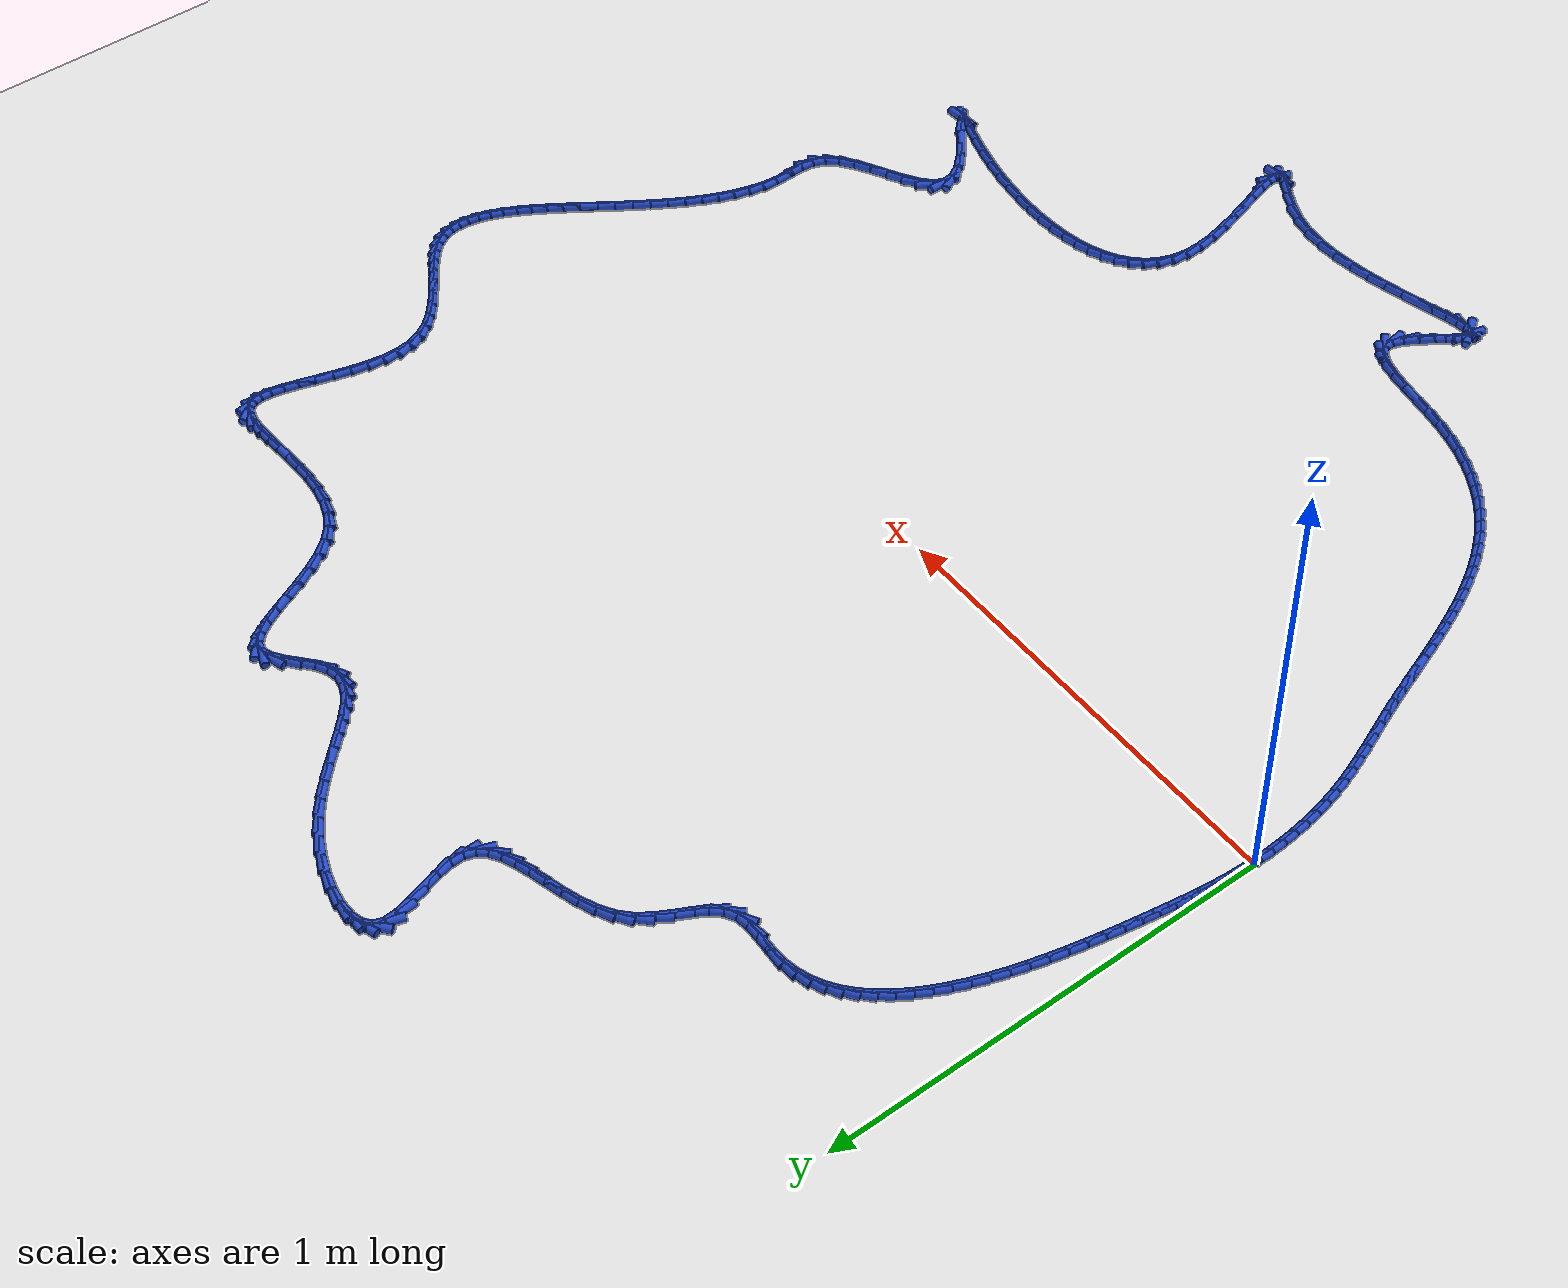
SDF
<sdf version="1.6">
 <world name="default">
  <light name="sun" type="directional">
   <pose>0 0 10 0 -0 0</pose>
   <diffuse>0.8 0.8 0.8 1</diffuse>
   <specular>0.2 0.2 0.2 1</specular>
   <attenuation>
    <range>1000</range>
    <constant>0.9</constant>
    <linear>0.01</linear>
    <quadratic>0.001</quadratic>
   </attenuation>
   <direction>-0.5 0.1 -0.9</direction>
  </light>
  <model name="ground_plane">
   <static>1</static>
   <link name="link">
    <collision name="collision">
     <geometry><plane><normal>0 0 1</normal><size>100 100</size></plane></geometry>
     <surface><friction><ode><mu>100</mu><mu2>50</mu2></ode></friction></surface>
    </collision>
    <visual name="visual">
     <cast_shadows>0</cast_shadows>
     <geometry><plane><normal>0 0 1</normal><size>100 100</size></plane></geometry>
     <material>
      <script><uri>file://media/materials/scripts/gazebo.material</uri><name>Gazebo/WhiteGlow</name></script>
     </material>
    </visual>
   </link>
  </model>
  <gravity>0 0 -9.8</gravity>
  <magnetic_field>6e-06 2.3e-05 -4.2e-05</magnetic_field>
  <atmosphere type="adiabatic"/>
  <physics name="default_physics" default="0" type="ode">
   <max_step_size>0.001</max_step_size>
   <real_time_factor>1</real_time_factor>
   <real_time_update_rate>1000</real_time_update_rate>
  </physics>
  <scene><ambient>0.4 0.4 0.4 1</ambient><background>0.7 0.7 0.7 1</background><shadows>1</shadows></scene>
  <spherical_coordinates>
   <surface_model>EARTH_WGS84</surface_model>
   <latitude_deg>0</latitude_deg>
   <longitude_deg>0</longitude_deg>
   <elevation>0</elevation>
   <heading_deg>0</heading_deg>
  </spherical_coordinates>
  <model name="line">
   <link name="link_0">
    <pose>-4.336808689942018e-18 6.938893903907228e-18 0.01 0 1.57 1.5356205352324663</pose>
    <collision name="collision">
     <geometry><cylinder><radius>0.01</radius><length>0.08</length></cylinder></geometry>
    </collision>
    <visual name="visual">
     <material>
      <script><name>Gazebo/Blue</name><uri>file://media/materials/scripts/gazebo.material</uri></script>
     </material>
     <geometry><cylinder><radius>0.01</radius><length>0.08</length></cylinder></geometry>
    </visual>
   </link>
   <link name="link_1">
    <pose>0.0011072280833253991 0.03146400764045911 0.01 0 1.57 1.5025603807263712</pose>
    <collision name="collision">
     <geometry><cylinder><radius>0.01</radius><length>0.08</length></cylinder></geometry>
    </collision>
    <visual name="visual">
     <material>
      <script><name>Gazebo/Blue</name><uri>file://media/materials/scripts/gazebo.material</uri></script>
     </material>
     <geometry><cylinder><radius>0.01</radius><length>0.08</length></cylinder></geometry>
    </visual>
   </link>
   <link name="link_2">
    <pose>0.003242141381773186 0.06270265682923397 0.01 0 1.57 1.4731487438103383</pose>
    <collision name="collision">
     <geometry><cylinder><radius>0.01</radius><length>0.08</length></cylinder></geometry>
    </collision>
    <visual name="visual">
     <material>
      <script><name>Gazebo/Blue</name><uri>file://media/materials/scripts/gazebo.material</uri></script>
     </material>
     <geometry><cylinder><radius>0.01</radius><length>0.08</length></cylinder></geometry>
    </visual>
   </link>
   <link name="link_3">
    <pose>0.006304133384892417 0.09396050914934653 0.01 0 1.57 1.4480577535225045</pose>
    <collision name="collision">
     <geometry><cylinder><radius>0.01</radius><length>0.08</length></cylinder></geometry>
    </collision>
    <visual name="visual">
     <material>
      <script><name>Gazebo/Blue</name><uri>file://media/materials/scripts/gazebo.material</uri></script>
     </material>
     <geometry><cylinder><radius>0.01</radius><length>0.08</length></cylinder></geometry>
    </visual>
   </link>
   <link name="link_4">
    <pose>0.010192597582232144 0.12548212618381874 0.01 0 1.57 1.4277177274706903</pose>
    <collision name="collision">
     <geometry><cylinder><radius>0.01</radius><length>0.08</length></cylinder></geometry>
    </collision>
    <visual name="visual">
     <material>
      <script><name>Gazebo/Blue</name><uri>file://media/materials/scripts/gazebo.material</uri></script>
     </material>
     <geometry><cylinder><radius>0.01</radius><length>0.08</length></cylinder></geometry>
    </visual>
   </link>
   <link name="link_5">
    <pose>0.014806927463341436 0.1575120695156726 0.01 0 1.57 1.4123095281165876</pose>
    <collision name="collision">
     <geometry><cylinder><radius>0.01</radius><length>0.08</length></cylinder></geometry>
    </collision>
    <visual name="visual">
     <material>
      <script><name>Gazebo/Blue</name><uri>file://media/materials/scripts/gazebo.material</uri></script>
     </material>
     <geometry><cylinder><radius>0.01</radius><length>0.08</length></cylinder></geometry>
    </visual>
   </link>
   <link name="link_6">
    <pose>0.020046516517769362 0.19029490072793018 0.01 0 1.57 1.401784941963018</pose>
    <collision name="collision">
     <geometry><cylinder><radius>0.01</radius><length>0.08</length></cylinder></geometry>
    </collision>
    <visual name="visual">
     <material>
      <script><name>Gazebo/Blue</name><uri>file://media/materials/scripts/gazebo.material</uri></script>
     </material>
     <geometry><cylinder><radius>0.01</radius><length>0.08</length></cylinder></geometry>
    </visual>
   </link>
   <link name="link_7">
    <pose>0.025810758235064953 0.22407518140361318 0.01 0 1.57 1.395241329125998</pose>
    <collision name="collision">
     <geometry><cylinder><radius>0.01</radius><length>0.08</length></cylinder></geometry>
    </collision>
    <visual name="visual">
     <material>
      <script><name>Gazebo/Blue</name><uri>file://media/materials/scripts/gazebo.material</uri></script>
     </material>
     <geometry><cylinder><radius>0.01</radius><length>0.08</length></cylinder></geometry>
    </visual>
   </link>
   <link name="link_8">
    <pose>0.03201500032406496 0.2590521031463418 0.01 0 1.57 1.3877374541404384</pose>
    <collision name="collision">
     <geometry><cylinder><radius>0.01</radius><length>0.08</length></cylinder></geometry>
    </collision>
    <visual name="visual">
     <material>
      <script><name>Gazebo/Blue</name><uri>file://media/materials/scripts/gazebo.material</uri></script>
     </material>
     <geometry><cylinder><radius>0.01</radius><length>0.08</length></cylinder></geometry>
    </visual>
   </link>
   <link name="link_9">
    <pose>0.038688677898970535 0.2951004202972108 0.01 0 1.57 1.3772761028116924</pose>
    <collision name="collision">
     <geometry><cylinder><radius>0.01</radius><length>0.08</length></cylinder></geometry>
    </collision>
    <visual name="visual">
     <material>
      <script><name>Gazebo/Blue</name><uri>file://media/materials/scripts/gazebo.material</uri></script>
     </material>
     <geometry><cylinder><radius>0.01</radius><length>0.08</length></cylinder></geometry>
    </visual>
   </link>
   <link name="link_10">
    <pose>0.04591090136471561 0.33195362256526384 0.01 0 1.57 1.3638559900483838</pose>
    <collision name="collision">
     <geometry><cylinder><radius>0.01</radius><length>0.08</length></cylinder></geometry>
    </collision>
    <visual name="visual">
     <material>
      <script><name>Gazebo/Blue</name><uri>file://media/materials/scripts/gazebo.material</uri></script>
     </material>
     <geometry><cylinder><radius>0.01</radius><length>0.08</length></cylinder></geometry>
    </visual>
   </link>
   <link name="link_11">
    <pose>0.053760985821885744 0.36934461755412595 0.01 0 1.57 1.3473756674026995</pose>
    <collision name="collision">
     <geometry><cylinder><radius>0.01</radius><length>0.08</length></cylinder></geometry>
    </collision>
    <visual name="visual">
     <material>
      <script><name>Gazebo/Blue</name><uri>file://media/materials/scripts/gazebo.material</uri></script>
     </material>
     <geometry><cylinder><radius>0.01</radius><length>0.08</length></cylinder></geometry>
    </visual>
   </link>
   <link name="link_12">
    <pose>0.062318246371066525 0.407006312867422 0.01 0 1.57 1.3276319570948611</pose>
    <collision name="collision">
     <geometry><cylinder><radius>0.01</radius><length>0.08</length></cylinder></geometry>
    </collision>
    <visual name="visual">
     <material>
      <script><name>Gazebo/Blue</name><uri>file://media/materials/scripts/gazebo.material</uri></script>
     </material>
     <geometry><cylinder><radius>0.01</radius><length>0.08</length></cylinder></geometry>
    </visual>
   </link>
   <link name="link_13">
    <pose>0.0716619981128435 0.44467161610877715 0.01 0 1.57 1.3043187774488274</pose>
    <collision name="collision">
     <geometry><cylinder><radius>0.01</radius><length>0.08</length></cylinder></geometry>
    </collision>
    <visual name="visual">
     <material>
      <script><name>Gazebo/Blue</name><uri>file://media/materials/scripts/gazebo.material</uri></script>
     </material>
     <geometry><cylinder><radius>0.01</radius><length>0.08</length></cylinder></geometry>
    </visual>
   </link>
   <link name="link_14">
    <pose>0.08187155614780228 0.48207343488181603 0.01 0 1.57 1.2770194887863693</pose>
    <collision name="collision">
     <geometry><cylinder><radius>0.01</radius><length>0.08</length></cylinder></geometry>
    </collision>
    <visual name="visual">
     <material>
      <script><name>Gazebo/Blue</name><uri>file://media/materials/scripts/gazebo.material</uri></script>
     </material>
     <geometry><cylinder><radius>0.01</radius><length>0.08</length></cylinder></geometry>
    </visual>
   </link>
   <link name="link_15">
    <pose>0.09302623557652838 0.518944676790164 0.01 0 1.57 1.2451938332940118</pose>
    <collision name="collision">
     <geometry><cylinder><radius>0.01</radius><length>0.08</length></cylinder></geometry>
    </collision>
    <visual name="visual">
     <material>
      <script><name>Gazebo/Blue</name><uri>file://media/materials/scripts/gazebo.material</uri></script>
     </material>
     <geometry><cylinder><radius>0.01</radius><length>0.08</length></cylinder></geometry>
    </visual>
   </link>
   <link name="link_16">
    <pose>0.10520535149960741 0.5550182494374458 0.01 0 1.57 1.20816061359871</pose>
    <collision name="collision">
     <geometry><cylinder><radius>0.01</radius><length>0.08</length></cylinder></geometry>
    </collision>
    <visual name="visual">
     <material>
      <script><name>Gazebo/Blue</name><uri>file://media/materials/scripts/gazebo.material</uri></script>
     </material>
     <geometry><cylinder><radius>0.01</radius><length>0.08</length></cylinder></geometry>
    </visual>
   </link>
   <link name="link_17">
    <pose>0.11848821901762494 0.5900270604272866 0.01 0 1.57 1.1650781755119517</pose>
    <collision name="collision">
     <geometry><cylinder><radius>0.01</radius><length>0.08</length></cylinder></geometry>
    </collision>
    <visual name="visual">
     <material>
      <script><name>Gazebo/Blue</name><uri>file://media/materials/scripts/gazebo.material</uri></script>
     </material>
     <geometry><cylinder><radius>0.01</radius><length>0.08</length></cylinder></geometry>
    </visual>
   </link>
   <link name="link_18">
    <pose>0.1329541532311665 0.623704017363311 0.01 0 1.57 1.1149270377797056</pose>
    <collision name="collision">
     <geometry><cylinder><radius>0.01</radius><length>0.08</length></cylinder></geometry>
    </collision>
    <visual name="visual">
     <material>
      <script><name>Gazebo/Blue</name><uri>file://media/materials/scripts/gazebo.material</uri></script>
     </material>
     <geometry><cylinder><radius>0.01</radius><length>0.08</length></cylinder></geometry>
    </visual>
   </link>
   <link name="link_19">
    <pose>0.1486824692408177 0.6557820278491443 0.01 0 1.57 1.0565035398696607</pose>
    <collision name="collision">
     <geometry><cylinder><radius>0.01</radius><length>0.08</length></cylinder></geometry>
    </collision>
    <visual name="visual">
     <material>
      <script><name>Gazebo/Blue</name><uri>file://media/materials/scripts/gazebo.material</uri></script>
     </material>
     <geometry><cylinder><radius>0.01</radius><length>0.08</length></cylinder></geometry>
    </visual>
   </link>
   <link name="link_20">
    <pose>0.16575248214716407 0.6859939994884112 0.01 0 1.57 0.9884413628576164</pose>
    <collision name="collision">
     <geometry><cylinder><radius>0.01</radius><length>0.08</length></cylinder></geometry>
    </collision>
    <visual name="visual">
     <material>
      <script><name>Gazebo/Blue</name><uri>file://media/materials/scripts/gazebo.material</uri></script>
     </material>
     <geometry><cylinder><radius>0.01</radius><length>0.08</length></cylinder></geometry>
    </visual>
   </link>
   <link name="link_21">
    <pose>0.18424350705079126 0.714072839884737 0.01 0 1.57 0.9092900071972095</pose>
    <collision name="collision">
     <geometry><cylinder><radius>0.01</radius><length>0.08</length></cylinder></geometry>
    </collision>
    <visual name="visual">
     <material>
      <script><name>Gazebo/Blue</name><uri>file://media/materials/scripts/gazebo.material</uri></script>
     </material>
     <geometry><cylinder><radius>0.01</radius><length>0.08</length></cylinder></geometry>
    </visual>
   </link>
   <link name="link_22">
    <pose>0.20423485905228478 0.7397514566417465 0.01 0 1.57 0.8176936238280965</pose>
    <collision name="collision">
     <geometry><cylinder><radius>0.01</radius><length>0.08</length></cylinder></geometry>
    </collision>
    <visual name="visual">
     <material>
      <script><name>Gazebo/Blue</name><uri>file://media/materials/scripts/gazebo.material</uri></script>
     </material>
     <geometry><cylinder><radius>0.01</radius><length>0.08</length></cylinder></geometry>
    </visual>
   </link>
   <link name="link_23">
    <pose>0.22580585325223013 0.7627627573630646 0.01 0 1.57 0.7127189926959602</pose>
    <collision name="collision">
     <geometry><cylinder><radius>0.01</radius><length>0.08</length></cylinder></geometry>
    </collision>
    <visual name="visual">
     <material>
      <script><name>Gazebo/Blue</name><uri>file://media/materials/scripts/gazebo.material</uri></script>
     </material>
     <geometry><cylinder><radius>0.01</radius><length>0.08</length></cylinder></geometry>
    </visual>
   </link>
   <link name="link_24">
    <pose>0.249035804751213 0.7828396496523163 0.01 0 1.57 0.5943503504112714</pose>
    <collision name="collision">
     <geometry><cylinder><radius>0.01</radius><length>0.08</length></cylinder></geometry>
    </collision>
    <visual name="visual">
     <material>
      <script><name>Gazebo/Blue</name><uri>file://media/materials/scripts/gazebo.material</uri></script>
     </material>
     <geometry><cylinder><radius>0.01</radius><length>0.08</length></cylinder></geometry>
    </visual>
   </link>
   <link name="link_25">
    <pose>0.27400402864981904 0.7997150411131269 0.01 0 1.57 0.46406244516968975</pose>
    <collision name="collision">
     <geometry><cylinder><radius>0.01</radius><length>0.08</length></cylinder></geometry>
    </collision>
    <visual name="visual">
     <material>
      <script><name>Gazebo/Blue</name><uri>file://media/materials/scripts/gazebo.material</uri></script>
     </material>
     <geometry><cylinder><radius>0.01</radius><length>0.08</length></cylinder></geometry>
    </visual>
   </link>
   <link name="link_26">
    <pose>0.3007898400486335 0.8131218393491207 0.01 0 1.57 0.32520464031983815</pose>
    <collision name="collision">
     <geometry><cylinder><radius>0.01</radius><length>0.08</length></cylinder></geometry>
    </collision>
    <visual name="visual">
     <material>
      <script><name>Gazebo/Blue</name><uri>file://media/materials/scripts/gazebo.material</uri></script>
     </material>
     <geometry><cylinder><radius>0.01</radius><length>0.08</length></cylinder></geometry>
    </visual>
   </link>
   <link name="link_27">
    <pose>0.32947255404824244 0.8227929519639237 0.01 0 1.57 0.18281924524928075</pose>
    <collision name="collision">
     <geometry><cylinder><radius>0.01</radius><length>0.08</length></cylinder></geometry>
    </collision>
    <visual name="visual">
     <material>
      <script><name>Gazebo/Blue</name><uri>file://media/materials/scripts/gazebo.material</uri></script>
     </material>
     <geometry><cylinder><radius>0.01</radius><length>0.08</length></cylinder></geometry>
    </visual>
   </link>
   <link name="link_28">
    <pose>0.36013148574923093 0.8284612865611597 0.01 0 1.57 0.04279982451097071</pose>
    <collision name="collision">
     <geometry><cylinder><radius>0.01</radius><length>0.08</length></cylinder></geometry>
    </collision>
    <visual name="visual">
     <material>
      <script><name>Gazebo/Blue</name><uri>file://media/materials/scripts/gazebo.material</uri></script>
     </material>
     <geometry><cylinder><radius>0.01</radius><length>0.08</length></cylinder></geometry>
    </visual>
   </link>
   <link name="link_29">
    <pose>0.3928445751106963 0.8298622565934949 0.01 0 1.57 -0.05627389448336072</pose>
    <collision name="collision">
     <geometry><cylinder><radius>0.01</radius><length>0.08</length></cylinder></geometry>
    </collision>
    <visual name="visual">
     <material>
      <script><name>Gazebo/Blue</name><uri>file://media/materials/scripts/gazebo.material</uri></script>
     </material>
     <geometry><cylinder><radius>0.01</radius><length>0.08</length></cylinder></geometry>
    </visual>
   </link>
   <link name="link_30">
    <pose>0.4270283291488365 0.8279365704734921 0.01 0 1.57 -0.035244935165371374</pose>
    <collision name="collision">
     <geometry><cylinder><radius>0.01</radius><length>0.08</length></cylinder></geometry>
    </collision>
    <visual name="visual">
     <material>
      <script><name>Gazebo/Blue</name><uri>file://media/materials/scripts/gazebo.material</uri></script>
     </material>
     <geometry><cylinder><radius>0.01</radius><length>0.08</length></cylinder></geometry>
    </visual>
   </link>
   <link name="link_31">
    <pose>0.46037845528958515 0.8267606604923128 0.01 0 1.57 0.1378733718860252</pose>
    <collision name="collision">
     <geometry><cylinder><radius>0.01</radius><length>0.08</length></cylinder></geometry>
    </collision>
    <visual name="visual">
     <material>
      <script><name>Gazebo/Blue</name><uri>file://media/materials/scripts/gazebo.material</uri></script>
     </material>
     <geometry><cylinder><radius>0.01</radius><length>0.08</length></cylinder></geometry>
    </visual>
   </link>
   <link name="link_32">
    <pose>0.4903143958982589 0.8309143824381386 0.01 0 1.57 0.4996409974126413</pose>
    <collision name="collision">
     <geometry><cylinder><radius>0.01</radius><length>0.08</length></cylinder></geometry>
    </collision>
    <visual name="visual">
     <material>
      <script><name>Gazebo/Blue</name><uri>file://media/materials/scripts/gazebo.material</uri></script>
     </material>
     <geometry><cylinder><radius>0.01</radius><length>0.08</length></cylinder></geometry>
    </visual>
   </link>
   <link name="link_33">
    <pose>0.5147231740895354 0.8442375829235944 0.01 0 1.57 0.832716780601831</pose>
    <collision name="collision">
     <geometry><cylinder><radius>0.01</radius><length>0.08</length></cylinder></geometry>
    </collision>
    <visual name="visual">
     <material>
      <script><name>Gazebo/Blue</name><uri>file://media/materials/scripts/gazebo.material</uri></script>
     </material>
     <geometry><cylinder><radius>0.01</radius><length>0.08</length></cylinder></geometry>
    </visual>
   </link>
   <link name="link_34">
    <pose>0.5344361363996283 0.8659103223089525 0.01 0 1.57 1.0155939138871395</pose>
    <collision name="collision">
     <geometry><cylinder><radius>0.01</radius><length>0.08</length></cylinder></geometry>
    </collision>
    <visual name="visual">
     <material>
      <script><name>Gazebo/Blue</name><uri>file://media/materials/scripts/gazebo.material</uri></script>
     </material>
     <geometry><cylinder><radius>0.01</radius><length>0.08</length></cylinder></geometry>
    </visual>
   </link>
   <link name="link_35">
    <pose>0.5514277539226377 0.8933035132023726 0.01 0 1.57 1.081069436491082</pose>
    <collision name="collision">
     <geometry><cylinder><radius>0.01</radius><length>0.08</length></cylinder></geometry>
    </collision>
    <visual name="visual">
     <material>
      <script><name>Gazebo/Blue</name><uri>file://media/materials/scripts/gazebo.material</uri></script>
     </material>
     <geometry><cylinder><radius>0.01</radius><length>0.08</length></cylinder></geometry>
    </visual>
   </link>
   <link name="link_36">
    <pose>0.5676750274360902 0.9237840646491008 0.01 0 1.57 1.0564667483142345</pose>
    <collision name="collision">
     <geometry><cylinder><radius>0.01</radius><length>0.08</length></cylinder></geometry>
    </collision>
    <visual name="visual">
     <material>
      <script><name>Gazebo/Blue</name><uri>file://media/materials/scripts/gazebo.material</uri></script>
     </material>
     <geometry><cylinder><radius>0.01</radius><length>0.08</length></cylinder></geometry>
    </visual>
   </link>
   <link name="link_37">
    <pose>0.5851549577175131 0.9547188856943832 0.01 0 1.57 0.947110756154163</pose>
    <collision name="collision">
     <geometry><cylinder><radius>0.01</radius><length>0.08</length></cylinder></geometry>
    </collision>
    <visual name="visual">
     <material>
      <script><name>Gazebo/Blue</name><uri>file://media/materials/scripts/gazebo.material</uri></script>
     </material>
     <geometry><cylinder><radius>0.01</radius><length>0.08</length></cylinder></geometry>
    </visual>
   </link>
   <link name="link_38">
    <pose>0.6058445455444328 0.9834748853834654 0.01 0 1.57 0.7520872696079361</pose>
    <collision name="collision">
     <geometry><cylinder><radius>0.01</radius><length>0.08</length></cylinder></geometry>
    </collision>
    <visual name="visual">
     <material>
      <script><name>Gazebo/Blue</name><uri>file://media/materials/scripts/gazebo.material</uri></script>
     </material>
     <geometry><cylinder><radius>0.01</radius><length>0.08</length></cylinder></geometry>
    </visual>
   </link>
   <link name="link_39">
    <pose>0.6315903774653531 1.0075601835910943 0.01 0 1.57 0.5527249260086872</pose>
    <collision name="collision">
     <geometry><cylinder><radius>0.01</radius><length>0.08</length></cylinder></geometry>
    </collision>
    <visual name="visual">
     <material>
      <script><name>Gazebo/Blue</name><uri>file://media/materials/scripts/gazebo.material</uri></script>
     </material>
     <geometry><cylinder><radius>0.01</radius><length>0.08</length></cylinder></geometry>
    </visual>
   </link>
   <link name="link_40">
    <pose>0.66234631790809 1.0265323150655166 0.01 0 1.57 0.411415885465258</pose>
    <collision name="collision">
     <geometry><cylinder><radius>0.01</radius><length>0.08</length></cylinder></geometry>
    </collision>
    <visual name="visual">
     <material>
      <script><name>Gazebo/Blue</name><uri>file://media/materials/scripts/gazebo.material</uri></script>
     </material>
     <geometry><cylinder><radius>0.01</radius><length>0.08</length></cylinder></geometry>
    </visual>
   </link>
   <link name="link_41">
    <pose>0.6966386412262948 1.041494590503429 0.01 0 1.57 0.3214297564279859</pose>
    <collision name="collision">
     <geometry><cylinder><radius>0.01</radius><length>0.08</length></cylinder></geometry>
    </collision>
    <visual name="visual">
     <material>
      <script><name>Gazebo/Blue</name><uri>file://media/materials/scripts/gazebo.material</uri></script>
     </material>
     <geometry><cylinder><radius>0.01</radius><length>0.08</length></cylinder></geometry>
    </visual>
   </link>
   <link name="link_42">
    <pose>0.7329585596513939 1.0535882854110454 0.01 0 1.57 0.2743057573226183</pose>
    <collision name="collision">
     <geometry><cylinder><radius>0.01</radius><length>0.08</length></cylinder></geometry>
    </collision>
    <visual name="visual">
     <material>
      <script><name>Gazebo/Blue</name><uri>file://media/materials/scripts/gazebo.material</uri></script>
     </material>
     <geometry><cylinder><radius>0.01</radius><length>0.08</length></cylinder></geometry>
    </visual>
   </link>
   <link name="link_43">
    <pose>0.7697972854148135 1.063954675294581 0.01 0 1.57 0.26634109811476325</pose>
    <collision name="collision">
     <geometry><cylinder><radius>0.01</radius><length>0.08</length></cylinder></geometry>
    </collision>
    <visual name="visual">
     <material>
      <script><name>Gazebo/Blue</name><uri>file://media/materials/scripts/gazebo.material</uri></script>
     </material>
     <geometry><cylinder><radius>0.01</radius><length>0.08</length></cylinder></geometry>
    </visual>
   </link>
   <link name="link_44">
    <pose>0.80564603074798 1.0737350356602504 0.01 0 1.57 0.30052670313236807</pose>
    <collision name="collision">
     <geometry><cylinder><radius>0.01</radius><length>0.08</length></cylinder></geometry>
    </collision>
    <visual name="visual">
     <material>
      <script><name>Gazebo/Blue</name><uri>file://media/materials/scripts/gazebo.material</uri></script>
     </material>
     <geometry><cylinder><radius>0.01</radius><length>0.08</length></cylinder></geometry>
    </visual>
   </link>
   <link name="link_45">
    <pose>0.8389960078823196 1.0840706420142678 0.01 0 1.57 0.38914785512775685</pose>
    <collision name="collision">
     <geometry><cylinder><radius>0.01</radius><length>0.08</length></cylinder></geometry>
    </collision>
    <visual name="visual">
     <material>
      <script><name>Gazebo/Blue</name><uri>file://media/materials/scripts/gazebo.material</uri></script>
     </material>
     <geometry><cylinder><radius>0.01</radius><length>0.08</length></cylinder></geometry>
    </visual>
   </link>
   <link name="link_46">
    <pose>0.8683384290492588 1.0961027698628483 0.01 0 1.57 0.5579539746519782</pose>
    <collision name="collision">
     <geometry><cylinder><radius>0.01</radius><length>0.08</length></cylinder></geometry>
    </collision>
    <visual name="visual">
     <material>
      <script><name>Gazebo/Blue</name><uri>file://media/materials/scripts/gazebo.material</uri></script>
     </material>
     <geometry><cylinder><radius>0.01</radius><length>0.08</length></cylinder></geometry>
    </visual>
   </link>
   <link name="link_47">
    <pose>0.8921645064802244 1.1109726947122063 0.01 0 1.57 0.8427840264961198</pose>
    <collision name="collision">
     <geometry><cylinder><radius>0.01</radius><length>0.08</length></cylinder></geometry>
    </collision>
    <visual name="visual">
     <material>
      <script><name>Gazebo/Blue</name><uri>file://media/materials/scripts/gazebo.material</uri></script>
     </material>
     <geometry><cylinder><radius>0.01</radius><length>0.08</length></cylinder></geometry>
    </visual>
   </link>
   <link name="link_48">
    <pose>0.9089654524066428 1.1298216920685566 0.01 0 1.57 1.2386689034204432</pose>
    <collision name="collision">
     <geometry><cylinder><radius>0.01</radius><length>0.08</length></cylinder></geometry>
    </collision>
    <visual name="visual">
     <material>
      <script><name>Gazebo/Blue</name><uri>file://media/materials/scripts/gazebo.material</uri></script>
     </material>
     <geometry><cylinder><radius>0.01</radius><length>0.08</length></cylinder></geometry>
    </visual>
   </link>
   <link name="link_49">
    <pose>0.9172325496287662 1.1537909885401658 0.01 0 1.57 -1.5411900693138265</pose>
    <collision name="collision">
     <geometry><cylinder><radius>0.01</radius><length>0.08</length></cylinder></geometry>
    </collision>
    <visual name="visual">
     <material>
      <script><name>Gazebo/Blue</name><uri>file://media/materials/scripts/gazebo.material</uri></script>
     </material>
     <geometry><cylinder><radius>0.01</radius><length>0.08</length></cylinder></geometry>
    </visual>
   </link>
   <link name="link_50">
    <pose>0.9163557067880118 1.1833991425996107 0.01 0 1.57 -1.351472387062178</pose>
    <collision name="collision">
     <geometry><cylinder><radius>0.01</radius><length>0.08</length></cylinder></geometry>
    </collision>
    <visual name="visual">
     <material>
      <script><name>Gazebo/Blue</name><uri>file://media/materials/scripts/gazebo.material</uri></script>
     </material>
     <geometry><cylinder><radius>0.01</radius><length>0.08</length></cylinder></geometry>
    </visual>
   </link>
   <link name="link_51">
    <pose>0.9088688264460544 1.216986203329609 0.01 0 1.57 -1.2729591687332182</pose>
    <collision name="collision">
     <geometry><cylinder><radius>0.01</radius><length>0.08</length></cylinder></geometry>
    </collision>
    <visual name="visual">
     <material>
      <script><name>Gazebo/Blue</name><uri>file://media/materials/scripts/gazebo.material</uri></script>
     </material>
     <geometry><cylinder><radius>0.01</radius><length>0.08</length></cylinder></geometry>
    </visual>
   </link>
   <link name="link_52">
    <pose>0.897992991826425 1.252416064463231 0.01 0 1.57 -1.2662650251652474</pose>
    <collision name="collision">
     <geometry><cylinder><radius>0.01</radius><length>0.08</length></cylinder></geometry>
    </collision>
    <visual name="visual">
     <material>
      <script><name>Gazebo/Blue</name><uri>file://media/materials/scripts/gazebo.material</uri></script>
     </material>
     <geometry><cylinder><radius>0.01</radius><length>0.08</length></cylinder></geometry>
    </visual>
   </link>
   <link name="link_53">
    <pose>0.886949286152656 1.287552619733549 0.01 0 1.57 -1.3311855283755998</pose>
    <collision name="collision">
     <geometry><cylinder><radius>0.01</radius><length>0.08</length></cylinder></geometry>
    </collision>
    <visual name="visual">
     <material>
      <script><name>Gazebo/Blue</name><uri>file://media/materials/scripts/gazebo.material</uri></script>
     </material>
     <geometry><cylinder><radius>0.01</radius><length>0.08</length></cylinder></geometry>
    </visual>
   </link>
   <link name="link_54">
    <pose>0.8789587926482786 1.3202597628736326 0.01 0 1.57 -1.5098874312382555</pose>
    <collision name="collision">
     <geometry><cylinder><radius>0.01</radius><length>0.08</length></cylinder></geometry>
    </collision>
    <visual name="visual">
     <material>
      <script><name>Gazebo/Blue</name><uri>file://media/materials/scripts/gazebo.material</uri></script>
     </material>
     <geometry><cylinder><radius>0.01</radius><length>0.08</length></cylinder></geometry>
    </visual>
   </link>
   <link name="link_55">
    <pose>0.8772425945368248 1.348401387616554 0.01 0 1.57 1.2292846988651</pose>
    <collision name="collision">
     <geometry><cylinder><radius>0.01</radius><length>0.08</length></cylinder></geometry>
    </collision>
    <visual name="visual">
     <material>
      <script><name>Gazebo/Blue</name><uri>file://media/materials/scripts/gazebo.material</uri></script>
     </material>
     <geometry><cylinder><radius>0.01</radius><length>0.08</length></cylinder></geometry>
    </visual>
   </link>
   <link name="link_56">
    <pose>0.884888430947695 1.3699123802993478 0.01 0 1.57 0.6783259774967093</pose>
    <collision name="collision">
     <geometry><cylinder><radius>0.01</radius><length>0.08</length></cylinder></geometry>
    </collision>
    <visual name="visual">
     <material>
      <script><name>Gazebo/Blue</name><uri>file://media/materials/scripts/gazebo.material</uri></script>
     </material>
     <geometry><cylinder><radius>0.01</radius><length>0.08</length></cylinder></geometry>
    </visual>
   </link>
   <link name="link_57">
    <pose>0.9024586446941425 1.384072152201771 0.01 0 1.57 0.27535991538969545</pose>
    <collision name="collision">
     <geometry><cylinder><radius>0.01</radius><length>0.08</length></cylinder></geometry>
    </collision>
    <visual name="visual">
     <material>
      <script><name>Gazebo/Blue</name><uri>file://media/materials/scripts/gazebo.material</uri></script>
     </material>
     <geometry><cylinder><radius>0.01</radius><length>0.08</length></cylinder></geometry>
    </visual>
   </link>
   <link name="link_58">
    <pose>0.9282587639608674 1.3913616462363747 0.01 0 1.57 0.029209063441881608</pose>
    <collision name="collision">
     <geometry><cylinder><radius>0.01</radius><length>0.08</length></cylinder></geometry>
    </collision>
    <visual name="visual">
     <material>
      <script><name>Gazebo/Blue</name><uri>file://media/materials/scripts/gazebo.material</uri></script>
     </material>
     <geometry><cylinder><radius>0.01</radius><length>0.08</length></cylinder></geometry>
    </visual>
   </link>
   <link name="link_59">
    <pose>0.9605149021702744 1.3923040858591809 0.01 0 1.57 -0.13138865890692586</pose>
    <collision name="collision">
     <geometry><cylinder><radius>0.01</radius><length>0.08</length></cylinder></geometry>
    </collision>
    <visual name="visual">
     <material>
      <script><name>Gazebo/Blue</name><uri>file://media/materials/scripts/gazebo.material</uri></script>
     </material>
     <geometry><cylinder><radius>0.01</radius><length>0.08</length></cylinder></geometry>
    </visual>
   </link>
   <link name="link_60">
    <pose>0.9974531727447675 1.387422694526211 0.01 0 1.57 -0.2501769947388208</pose>
    <collision name="collision">
     <geometry><cylinder><radius>0.01</radius><length>0.08</length></cylinder></geometry>
    </collision>
    <visual name="visual">
     <material>
      <script><name>Gazebo/Blue</name><uri>file://media/materials/scripts/gazebo.material</uri></script>
     </material>
     <geometry><cylinder><radius>0.01</radius><length>0.08</length></cylinder></geometry>
    </visual>
   </link>
   <link name="link_61">
    <pose>1.037299689106752 1.3772406956934875 0.01 0 1.57 -0.35000421066758286</pose>
    <collision name="collision">
     <geometry><cylinder><radius>0.01</radius><length>0.08</length></cylinder></geometry>
    </collision>
    <visual name="visual">
     <material>
      <script><name>Gazebo/Blue</name><uri>file://media/materials/scripts/gazebo.material</uri></script>
     </material>
     <geometry><cylinder><radius>0.01</radius><length>0.08</length></cylinder></geometry>
    </visual>
   </link>
   <link name="link_62">
    <pose>1.0782805646786315 1.3622813128170315 0.01 0 1.57 -0.4444874581930824</pose>
    <collision name="collision">
     <geometry><cylinder><radius>0.01</radius><length>0.08</length></cylinder></geometry>
    </collision>
    <visual name="visual">
     <material>
      <script><name>Gazebo/Blue</name><uri>file://media/materials/scripts/gazebo.material</uri></script>
     </material>
     <geometry><cylinder><radius>0.01</radius><length>0.08</length></cylinder></geometry>
    </visual>
   </link>
   <link name="link_63">
    <pose>1.1186219128828112 1.3430677693528654 0.01 0 1.57 -0.5431550507498765</pose>
    <collision name="collision">
     <geometry><cylinder><radius>0.01</radius><length>0.08</length></cylinder></geometry>
    </collision>
    <visual name="visual">
     <material>
      <script><name>Gazebo/Blue</name><uri>file://media/materials/scripts/gazebo.material</uri></script>
     </material>
     <geometry><cylinder><radius>0.01</radius><length>0.08</length></cylinder></geometry>
    </visual>
   </link>
   <link name="link_64">
    <pose>1.156603375377673 1.320137354911235 0.01 0 1.57 -0.6361913903047263</pose>
    <collision name="collision">
     <geometry><cylinder><radius>0.01</radius><length>0.08</length></cylinder></geometry>
    </collision>
    <visual name="visual">
     <material>
      <script><name>Gazebo/Blue</name><uri>file://media/materials/scripts/gazebo.material</uri></script>
     </material>
     <geometry><cylinder><radius>0.01</radius><length>0.08</length></cylinder></geometry>
    </visual>
   </link>
   <link name="link_65">
    <pose>1.191572255167857 1.29430791923819 0.01 0 1.57 -0.708213836120784</pose>
    <collision name="collision">
     <geometry><cylinder><radius>0.01</radius><length>0.08</length></cylinder></geometry>
    </collision>
    <visual name="visual">
     <material>
      <script><name>Gazebo/Blue</name><uri>file://media/materials/scripts/gazebo.material</uri></script>
     </material>
     <geometry><cylinder><radius>0.01</radius><length>0.08</length></cylinder></geometry>
    </visual>
   </link>
   <link name="link_66">
    <pose>1.2238598890093935 1.266655896549373 0.01 0 1.57 -0.7582304636707654</pose>
    <collision name="collision">
     <geometry><cylinder><radius>0.01</radius><length>0.08</length></cylinder></geometry>
    </collision>
    <visual name="visual">
     <material>
      <script><name>Gazebo/Blue</name><uri>file://media/materials/scripts/gazebo.material</uri></script>
     </material>
     <geometry><cylinder><radius>0.01</radius><length>0.08</length></cylinder></geometry>
    </visual>
   </link>
   <link name="link_67">
    <pose>1.2538343814853161 1.2382673829130102 0.01 0 1.57 -0.785566757976279</pose>
    <collision name="collision">
     <geometry><cylinder><radius>0.01</radius><length>0.08</length></cylinder></geometry>
    </collision>
    <visual name="visual">
     <material>
      <script><name>Gazebo/Blue</name><uri>file://media/materials/scripts/gazebo.material</uri></script>
     </material>
     <geometry><cylinder><radius>0.01</radius><length>0.08</length></cylinder></geometry>
    </visual>
   </link>
   <link name="link_68">
    <pose>1.28186383717866 1.2102284743973273 0.01 0 1.57 -0.7882382605085606</pose>
    <collision name="collision">
     <geometry><cylinder><radius>0.01</radius><length>0.08</length></cylinder></geometry>
    </collision>
    <visual name="visual">
     <material>
      <script><name>Gazebo/Blue</name><uri>file://media/materials/scripts/gazebo.material</uri></script>
     </material>
     <geometry><cylinder><radius>0.01</radius><length>0.08</length></cylinder></geometry>
    </visual>
   </link>
   <link name="link_69">
    <pose>1.3083163606724577 1.1836252670705516 0.01 0 1.57 -0.7618387460049367</pose>
    <collision name="collision">
     <geometry><cylinder><radius>0.01</radius><length>0.08</length></cylinder></geometry>
    </collision>
    <visual name="visual">
     <material>
      <script><name>Gazebo/Blue</name><uri>file://media/materials/scripts/gazebo.material</uri></script>
     </material>
     <geometry><cylinder><radius>0.01</radius><length>0.08</length></cylinder></geometry>
    </visual>
   </link>
   <link name="link_70">
    <pose>1.333560056549744 1.1595438570009098 0.01 0 1.57 -0.6980593438315549</pose>
    <collision name="collision">
     <geometry><cylinder><radius>0.01</radius><length>0.08</length></cylinder></geometry>
    </collision>
    <visual name="visual">
     <material>
      <script><name>Gazebo/Blue</name><uri>file://media/materials/scripts/gazebo.material</uri></script>
     </material>
     <geometry><cylinder><radius>0.01</radius><length>0.08</length></cylinder></geometry>
    </visual>
   </link>
   <link name="link_71">
    <pose>1.3579630293935534 1.1390703402566276 0.01 0 1.57 -0.5829506277651483</pose>
    <collision name="collision">
     <geometry><cylinder><radius>0.01</radius><length>0.08</length></cylinder></geometry>
    </collision>
    <visual name="visual">
     <material>
      <script><name>Gazebo/Blue</name><uri>file://media/materials/scripts/gazebo.material</uri></script>
     </material>
     <geometry><cylinder><radius>0.01</radius><length>0.08</length></cylinder></geometry>
    </visual>
   </link>
   <link name="link_72">
    <pose>1.381893383786919 1.123290812905931 0.01 0 1.57 -0.39736355007476176</pose>
    <collision name="collision">
     <geometry><cylinder><radius>0.01</radius><length>0.08</length></cylinder></geometry>
    </collision>
    <visual name="visual">
     <material>
      <script><name>Gazebo/Blue</name><uri>file://media/materials/scripts/gazebo.material</uri></script>
     </material>
     <geometry><cylinder><radius>0.01</radius><length>0.08</length></cylinder></geometry>
    </visual>
   </link>
   <link name="link_73">
    <pose>1.4057192243128758 1.1132913710170473 0.01 0 1.57 -0.12934171890205653</pose>
    <collision name="collision">
     <geometry><cylinder><radius>0.01</radius><length>0.08</length></cylinder></geometry>
    </collision>
    <visual name="visual">
     <material>
      <script><name>Gazebo/Blue</name><uri>file://media/materials/scripts/gazebo.material</uri></script>
     </material>
     <geometry><cylinder><radius>0.01</radius><length>0.08</length></cylinder></geometry>
    </visual>
   </link>
   <link name="link_74">
    <pose>1.4298086555544565 1.1101581106582024 0.01 0 1.57 0.19252083070281928</pose>
    <collision name="collision">
     <geometry><cylinder><radius>0.01</radius><length>0.08</length></cylinder></geometry>
    </collision>
    <visual name="visual">
     <material>
      <script><name>Gazebo/Blue</name><uri>file://media/materials/scripts/gazebo.material</uri></script>
     </material>
     <geometry><cylinder><radius>0.01</radius><length>0.08</length></cylinder></geometry>
    </visual>
   </link>
   <link name="link_75">
    <pose>1.4545297820946967 1.114977127897623 0.01 0 1.57 0.49342976665261934</pose>
    <collision name="collision">
     <geometry><cylinder><radius>0.01</radius><length>0.08</length></cylinder></geometry>
    </collision>
    <visual name="visual">
     <material>
      <script><name>Gazebo/Blue</name><uri>file://media/materials/scripts/gazebo.material</uri></script>
     </material>
     <geometry><cylinder><radius>0.01</radius><length>0.08</length></cylinder></geometry>
    </visual>
   </link>
   <link name="link_76">
    <pose>1.4802450763413812 1.128806859006717 0.01 0 1.57 0.6768735097541512</pose>
    <collision name="collision">
     <geometry><cylinder><radius>0.01</radius><length>0.08</length></cylinder></geometry>
    </collision>
    <visual name="visual">
     <material>
      <script><name>Gazebo/Blue</name><uri>file://media/materials/scripts/gazebo.material</uri></script>
     </material>
     <geometry><cylinder><radius>0.01</radius><length>0.08</length></cylinder></geometry>
    </visual>
   </link>
   <link name="link_77">
    <pose>1.5067944361874352 1.1501393597260332 0.01 0 1.57 0.7126994125406223</pose>
    <collision name="collision">
     <geometry><cylinder><radius>0.01</radius><length>0.08</length></cylinder></geometry>
    </collision>
    <visual name="visual">
     <material>
      <script><name>Gazebo/Blue</name><uri>file://media/materials/scripts/gazebo.material</uri></script>
     </material>
     <geometry><cylinder><radius>0.01</radius><length>0.08</length></cylinder></geometry>
    </visual>
   </link>
   <link name="link_78">
    <pose>1.5330787400544876 1.1728551304662964 0.01 0 1.57 0.6140378748856712</pose>
    <collision name="collision">
     <geometry><cylinder><radius>0.01</radius><length>0.08</length></cylinder></geometry>
    </collision>
    <visual name="visual">
     <material>
      <script><name>Gazebo/Blue</name><uri>file://media/materials/scripts/gazebo.material</uri></script>
     </material>
     <geometry><cylinder><radius>0.01</radius><length>0.08</length></cylinder></geometry>
    </visual>
   </link>
   <link name="link_79">
    <pose>1.557900867419528 1.1903533956165042 0.01 0 1.57 0.27306151013533486</pose>
    <collision name="collision">
     <geometry><cylinder><radius>0.01</radius><length>0.08</length></cylinder></geometry>
    </collision>
    <visual name="visual">
     <material>
      <script><name>Gazebo/Blue</name><uri>file://media/materials/scripts/gazebo.material</uri></script>
     </material>
     <geometry><cylinder><radius>0.01</radius><length>0.08</length></cylinder></geometry>
    </visual>
   </link>
   <link name="link_80">
    <pose>1.5801864595808888 1.1965946305407702 0.01 0 1.57 -0.28771847170197257</pose>
    <collision name="collision">
     <geometry><cylinder><radius>0.01</radius><length>0.08</length></cylinder></geometry>
    </collision>
    <visual name="visual">
     <material>
      <script><name>Gazebo/Blue</name><uri>file://media/materials/scripts/gazebo.material</uri></script>
     </material>
     <geometry><cylinder><radius>0.01</radius><length>0.08</length></cylinder></geometry>
    </visual>
   </link>
   <link name="link_81">
    <pose>1.5999969731963049 1.190732109724542 0.01 0 1.57 -0.7264145257541991</pose>
    <collision name="collision">
     <geometry><cylinder><radius>0.01</radius><length>0.08</length></cylinder></geometry>
    </collision>
    <visual name="visual">
     <material>
      <script><name>Gazebo/Blue</name><uri>file://media/materials/scripts/gazebo.material</uri></script>
     </material>
     <geometry><cylinder><radius>0.01</radius><length>0.08</length></cylinder></geometry>
    </visual>
   </link>
   <link name="link_82">
    <pose>1.6180085126071329 1.174729196392626 0.01 0 1.57 -0.9604016139994076</pose>
    <collision name="collision">
     <geometry><cylinder><radius>0.01</radius><length>0.08</length></cylinder></geometry>
    </collision>
    <visual name="visual">
     <material>
      <script><name>Gazebo/Blue</name><uri>file://media/materials/scripts/gazebo.material</uri></script>
     </material>
     <geometry><cylinder><radius>0.01</radius><length>0.08</length></cylinder></geometry>
    </visual>
   </link>
   <link name="link_83">
    <pose>1.634903222737844 1.1505768705249946 0.01 0 1.57 -1.073310563239943</pose>
    <collision name="collision">
     <geometry><cylinder><radius>0.01</radius><length>0.08</length></cylinder></geometry>
    </collision>
    <visual name="visual">
     <material>
      <script><name>Gazebo/Blue</name><uri>file://media/materials/scripts/gazebo.material</uri></script>
     </material>
     <geometry><cylinder><radius>0.01</radius><length>0.08</length></cylinder></geometry>
    </visual>
   </link>
   <link name="link_84">
    <pose>1.6513632485129093 1.1202661121016202 0.01 0 1.57 -1.1195598222980059</pose>
    <collision name="collision">
     <geometry><cylinder><radius>0.01</radius><length>0.08</length></cylinder></geometry>
    </collision>
    <visual name="visual">
     <material>
      <script><name>Gazebo/Blue</name><uri>file://media/materials/scripts/gazebo.material</uri></script>
     </material>
     <geometry><cylinder><radius>0.01</radius><length>0.08</length></cylinder></geometry>
    </visual>
   </link>
   <link name="link_85">
    <pose>1.6680707348568007 1.0857879011024745 0.01 0 1.57 -1.1223268118400533</pose>
    <collision name="collision">
     <geometry><cylinder><radius>0.01</radius><length>0.08</length></cylinder></geometry>
    </collision>
    <visual name="visual">
     <material>
      <script><name>Gazebo/Blue</name><uri>file://media/materials/scripts/gazebo.material</uri></script>
     </material>
     <geometry><cylinder><radius>0.01</radius><length>0.08</length></cylinder></geometry>
    </visual>
   </link>
   <link name="link_86">
    <pose>1.6857078266939896 1.0491332175075307 0.01 0 1.57 -1.0893143593907815</pose>
    <collision name="collision">
     <geometry><cylinder><radius>0.01</radius><length>0.08</length></cylinder></geometry>
    </collision>
    <visual name="visual">
     <material>
      <script><name>Gazebo/Blue</name><uri>file://media/materials/scripts/gazebo.material</uri></script>
     </material>
     <geometry><cylinder><radius>0.01</radius><length>0.08</length></cylinder></geometry>
    </visual>
   </link>
   <link name="link_87">
    <pose>1.7049566689489473 1.0122930412967608 0.01 0 1.57 -1.019494839847143</pose>
    <collision name="collision">
     <geometry><cylinder><radius>0.01</radius><length>0.08</length></cylinder></geometry>
    </collision>
    <visual name="visual">
     <material>
      <script><name>Gazebo/Blue</name><uri>file://media/materials/scripts/gazebo.material</uri></script>
     </material>
     <geometry><cylinder><radius>0.01</radius><length>0.08</length></cylinder></geometry>
    </visual>
   </link>
   <link name="link_88">
    <pose>1.7264994065461452 0.977258352450137 0.01 0 1.57 -0.9053327829608843</pose>
    <collision name="collision">
     <geometry><cylinder><radius>0.01</radius><length>0.08</length></cylinder></geometry>
    </collision>
    <visual name="visual">
     <material>
      <script><name>Gazebo/Blue</name><uri>file://media/materials/scripts/gazebo.material</uri></script>
     </material>
     <geometry><cylinder><radius>0.01</radius><length>0.08</length></cylinder></geometry>
    </visual>
   </link>
   <link name="link_89">
    <pose>1.7510181844100556 0.9460201309476319 0.01 0 1.57 -0.7347056852846849</pose>
    <collision name="collision">
     <geometry><cylinder><radius>0.01</radius><length>0.08</length></cylinder></geometry>
    </collision>
    <visual name="visual">
     <material>
      <script><name>Gazebo/Blue</name><uri>file://media/materials/scripts/gazebo.material</uri></script>
     </material>
     <geometry><cylinder><radius>0.01</radius><length>0.08</length></cylinder></geometry>
    </visual>
   </link>
   <link name="link_90">
    <pose>1.7791933573349288 0.9205658966634219 0.01 0 1.57 -0.5236528981676696</pose>
    <collision name="collision">
     <geometry><cylinder><radius>0.01</radius><length>0.08</length></cylinder></geometry>
    </collision>
    <visual name="visual">
     <material>
      <script><name>Gazebo/Blue</name><uri>file://media/materials/scripts/gazebo.material</uri></script>
     </material>
     <geometry><cylinder><radius>0.01</radius><length>0.08</length></cylinder></geometry>
    </visual>
   </link>
   <link name="link_91">
    <pose>1.8112709154444293 0.9020435949551331 0.01 0 1.57 -0.33770255946773026</pose>
    <collision name="collision">
     <geometry><cylinder><radius>0.01</radius><length>0.08</length></cylinder></geometry>
    </collision>
    <visual name="visual">
     <material>
      <script><name>Gazebo/Blue</name><uri>file://media/materials/scripts/gazebo.material</uri></script>
     </material>
     <geometry><cylinder><radius>0.01</radius><length>0.08</length></cylinder></geometry>
    </visual>
   </link>
   <link name="link_92">
    <pose>1.8464992892119563 0.8896730086989127 0.01 0 1.57 -0.19151743830005274</pose>
    <collision name="collision">
     <geometry><cylinder><radius>0.01</radius><length>0.08</length></cylinder></geometry>
    </collision>
    <visual name="visual">
     <material>
      <script><name>Gazebo/Blue</name><uri>file://media/materials/scripts/gazebo.material</uri></script>
     </material>
     <geometry><cylinder><radius>0.01</radius><length>0.08</length></cylinder></geometry>
    </visual>
   </link>
   <link name="link_93">
    <pose>1.88398741299645 0.8824042916072453 0.01 0 1.57 -0.082594951936038</pose>
    <collision name="collision">
     <geometry><cylinder><radius>0.01</radius><length>0.08</length></cylinder></geometry>
    </collision>
    <visual name="visual">
     <material>
      <script><name>Gazebo/Blue</name><uri>file://media/materials/scripts/gazebo.material</uri></script>
     </material>
     <geometry><cylinder><radius>0.01</radius><length>0.08</length></cylinder></geometry>
    </visual>
   </link>
   <link name="link_94">
    <pose>1.9228442211568515 0.8791875973926139 0.01 0 1.57 -0.00545363223273143</pose>
    <collision name="collision">
     <geometry><cylinder><radius>0.01</radius><length>0.08</length></cylinder></geometry>
    </collision>
    <visual name="visual">
     <material>
      <script><name>Gazebo/Blue</name><uri>file://media/materials/scripts/gazebo.material</uri></script>
     </material>
     <geometry><cylinder><radius>0.01</radius><length>0.08</length></cylinder></geometry>
    </visual>
   </link>
   <link name="link_95">
    <pose>1.9621786480521008 0.8789730797675025 0.01 0 1.57 0.044620130874636565</pose>
    <collision name="collision">
     <geometry><cylinder><radius>0.01</radius><length>0.08</length></cylinder></geometry>
    </collision>
    <visual name="visual">
     <material>
      <script><name>Gazebo/Blue</name><uri>file://media/materials/scripts/gazebo.material</uri></script>
     </material>
     <geometry><cylinder><radius>0.01</radius><length>0.08</length></cylinder></geometry>
    </visual>
   </link>
   <link name="link_96">
    <pose>2.00109962804114 0.8807108924443945 0.01 0 1.57 0.07007498911915154</pose>
    <collision name="collision">
     <geometry><cylinder><radius>0.01</radius><length>0.08</length></cylinder></geometry>
    </collision>
    <visual name="visual">
     <material>
      <script><name>Gazebo/Blue</name><uri>file://media/materials/scripts/gazebo.material</uri></script>
     </material>
     <geometry><cylinder><radius>0.01</radius><length>0.08</length></cylinder></geometry>
    </visual>
   </link>
   <link name="link_97">
    <pose>2.03871609548291 0.8833511891357735 0.01 0 1.57 0.07026448233679902</pose>
    <collision name="collision">
     <geometry><cylinder><radius>0.01</radius><length>0.08</length></cylinder></geometry>
    </collision>
    <visual name="visual">
     <material>
      <script><name>Gazebo/Blue</name><uri>file://media/materials/scripts/gazebo.material</uri></script>
     </material>
     <geometry><cylinder><radius>0.01</radius><length>0.08</length></cylinder></geometry>
    </visual>
   </link>
   <link name="link_98">
    <pose>2.074136984736351 0.8858441235541231 0.01 0 1.57 0.040051435700480364</pose>
    <collision name="collision">
     <geometry><cylinder><radius>0.01</radius><length>0.08</length></cylinder></geometry>
    </collision>
    <visual name="visual">
     <material>
      <script><name>Gazebo/Blue</name><uri>file://media/materials/scripts/gazebo.material</uri></script>
     </material>
     <geometry><cylinder><radius>0.01</radius><length>0.08</length></cylinder></geometry>
    </visual>
   </link>
   <link name="link_99">
    <pose>2.106471230160404 0.887139849411927 0.01 0 1.57 -0.03353626542487102</pose>
    <collision name="collision">
     <geometry><cylinder><radius>0.01</radius><length>0.08</length></cylinder></geometry>
    </collision>
    <visual name="visual">
     <material>
      <script><name>Gazebo/Blue</name><uri>file://media/materials/scripts/gazebo.material</uri></script>
     </material>
     <geometry><cylinder><radius>0.01</radius><length>0.08</length></cylinder></geometry>
    </visual>
   </link>
   <link name="link_100">
    <pose>2.1348277661140105 0.8861885204216685 0.01 0 1.57 -0.17893545830406263</pose>
    <collision name="collision">
     <geometry><cylinder><radius>0.01</radius><length>0.08</length></cylinder></geometry>
    </collision>
    <visual name="visual">
     <material>
      <script><name>Gazebo/Blue</name><uri>file://media/materials/scripts/gazebo.material</uri></script>
     </material>
     <geometry><cylinder><radius>0.01</radius><length>0.08</length></cylinder></geometry>
    </visual>
   </link>
   <link name="link_101">
    <pose>2.1583155269561107 0.8819402902958317 0.01 0 1.57 -0.4514358436486448</pose>
    <collision name="collision">
     <geometry><cylinder><radius>0.01</radius><length>0.08</length></cylinder></geometry>
    </collision>
    <visual name="visual">
     <material>
      <script><name>Gazebo/Blue</name><uri>file://media/materials/scripts/gazebo.material</uri></script>
     </material>
     <geometry><cylinder><radius>0.01</radius><length>0.08</length></cylinder></geometry>
    </visual>
   </link>
   <link name="link_102">
    <pose>2.176043447045646 0.8733453127468996 0.01 0 1.57 -0.9001134383795548</pose>
    <collision name="collision">
     <geometry><cylinder><radius>0.01</radius><length>0.08</length></cylinder></geometry>
    </collision>
    <visual name="visual">
     <material>
      <script><name>Gazebo/Blue</name><uri>file://media/materials/scripts/gazebo.material</uri></script>
     </material>
     <geometry><cylinder><radius>0.01</radius><length>0.08</length></cylinder></geometry>
    </visual>
   </link>
   <link name="link_103">
    <pose>2.18713429291404 0.8593658356881354 0.01 0 1.57 -1.3524003817196848</pose>
    <collision name="collision">
     <geometry><cylinder><radius>0.01</radius><length>0.08</length></cylinder></geometry>
    </collision>
    <visual name="visual">
     <material>
      <script><name>Gazebo/Blue</name><uri>file://media/materials/scripts/gazebo.material</uri></script>
     </material>
     <geometry><cylinder><radius>0.01</radius><length>0.08</length></cylinder></geometry>
    </visual>
   </link>
   <link name="link_104">
    <pose>2.191507560521084 0.839660729756795 0.01 0 1.57 1.5219206567587855</pose>
    <collision name="collision">
     <geometry><cylinder><radius>0.01</radius><length>0.08</length></cylinder></geometry>
    </collision>
    <visual name="visual">
     <material>
      <script><name>Gazebo/Blue</name><uri>file://media/materials/scripts/gazebo.material</uri></script>
     </material>
     <geometry><cylinder><radius>0.01</radius><length>0.08</length></cylinder></geometry>
    </visual>
   </link>
   <link name="link_105">
    <pose>2.190298955051684 0.814952261710799 0.01 0 1.57 1.3809874458709517</pose>
    <collision name="collision">
     <geometry><cylinder><radius>0.01</radius><length>0.08</length></cylinder></geometry>
    </collision>
    <visual name="visual">
     <material>
      <script><name>Gazebo/Blue</name><uri>file://media/materials/scripts/gazebo.material</uri></script>
     </material>
     <geometry><cylinder><radius>0.01</radius><length>0.08</length></cylinder></geometry>
    </visual>
   </link>
   <link name="link_106">
    <pose>2.1847466439241625 0.7860522864638533 0.01 0 1.57 1.3087498475771182</pose>
    <collision name="collision">
     <geometry><cylinder><radius>0.01</radius><length>0.08</length></cylinder></geometry>
    </collision>
    <visual name="visual">
     <material>
      <script><name>Gazebo/Blue</name><uri>file://media/materials/scripts/gazebo.material</uri></script>
     </material>
     <geometry><cylinder><radius>0.01</radius><length>0.08</length></cylinder></geometry>
    </visual>
   </link>
   <link name="link_107">
    <pose>2.176088794556841 0.753772658929664 0.01 0 1.57 1.2774715504518177</pose>
    <collision name="collision">
     <geometry><cylinder><radius>0.01</radius><length>0.08</length></cylinder></geometry>
    </collision>
    <visual name="visual">
     <material>
      <script><name>Gazebo/Blue</name><uri>file://media/materials/scripts/gazebo.material</uri></script>
     </material>
     <geometry><cylinder><radius>0.01</radius><length>0.08</length></cylinder></geometry>
    </visual>
   </link>
   <link name="link_108">
    <pose>2.165563574368041 0.7189252340219373 0.01 0 1.57 1.2749987658873705</pose>
    <collision name="collision">
     <geometry><cylinder><radius>0.01</radius><length>0.08</length></cylinder></geometry>
    </collision>
    <visual name="visual">
     <material>
      <script><name>Gazebo/Blue</name><uri>file://media/materials/scripts/gazebo.material</uri></script>
     </material>
     <geometry><cylinder><radius>0.01</radius><length>0.08</length></cylinder></geometry>
    </visual>
   </link>
   <link name="link_109">
    <pose>2.154409150776083 0.6823218666543788 0.01 0 1.57 1.2969932521439491</pose>
    <collision name="collision">
     <geometry><cylinder><radius>0.01</radius><length>0.08</length></cylinder></geometry>
    </collision>
    <visual name="visual">
     <material>
      <script><name>Gazebo/Blue</name><uri>file://media/materials/scripts/gazebo.material</uri></script>
     </material>
     <geometry><cylinder><radius>0.01</radius><length>0.08</length></cylinder></geometry>
    </visual>
   </link>
   <link name="link_110">
    <pose>2.14386369119929 0.6447744117406947 0.01 0 1.57 1.3439214933272465</pose>
    <collision name="collision">
     <geometry><cylinder><radius>0.01</radius><length>0.08</length></cylinder></geometry>
    </collision>
    <visual name="visual">
     <material>
      <script><name>Gazebo/Blue</name><uri>file://media/materials/scripts/gazebo.material</uri></script>
     </material>
     <geometry><cylinder><radius>0.01</radius><length>0.08</length></cylinder></geometry>
    </visual>
   </link>
   <link name="link_111">
    <pose>2.1351653630559815 0.6070947241945909 0.01 0 1.57 1.4202410493724342</pose>
    <collision name="collision">
     <geometry><cylinder><radius>0.01</radius><length>0.08</length></cylinder></geometry>
    </collision>
    <visual name="visual">
     <material>
      <script><name>Gazebo/Blue</name><uri>file://media/materials/scripts/gazebo.material</uri></script>
     </material>
     <geometry><cylinder><radius>0.01</radius><length>0.08</length></cylinder></geometry>
    </visual>
   </link>
   <link name="link_112">
    <pose>2.129552333764481 0.5700946589297733 0.01 0 1.57 1.5344953473322347</pose>
    <collision name="collision">
     <geometry><cylinder><radius>0.01</radius><length>0.08</length></cylinder></geometry>
    </collision>
    <visual name="visual">
     <material>
      <script><name>Gazebo/Blue</name><uri>file://media/materials/scripts/gazebo.material</uri></script>
     </material>
     <geometry><cylinder><radius>0.01</radius><length>0.08</length></cylinder></geometry>
    </visual>
   </link>
   <link name="link_113">
    <pose>2.1282627707431083 0.5345860708599487 0.01 0 1.57 -1.4428427610111758</pose>
    <collision name="collision">
     <geometry><cylinder><radius>0.01</radius><length>0.08</length></cylinder></geometry>
    </collision>
    <visual name="visual">
     <material>
      <script><name>Gazebo/Blue</name><uri>file://media/materials/scripts/gazebo.material</uri></script>
     </material>
     <geometry><cylinder><radius>0.01</radius><length>0.08</length></cylinder></geometry>
    </visual>
   </link>
   <link name="link_114">
    <pose>2.132534841410186 0.5013808148988219 0.01 0 1.57 -1.2225296229217635</pose>
    <collision name="collision">
     <geometry><cylinder><radius>0.01</radius><length>0.08</length></cylinder></geometry>
    </collision>
    <visual name="visual">
     <material>
      <script><name>Gazebo/Blue</name><uri>file://media/materials/scripts/gazebo.material</uri></script>
     </material>
     <geometry><cylinder><radius>0.01</radius><length>0.08</length></cylinder></geometry>
    </visual>
   </link>
   <link name="link_115">
    <pose>2.143482142351235 0.4712284004880938 0.01 0 1.57 -1.0036013262684376</pose>
    <collision name="collision">
     <geometry><cylinder><radius>0.01</radius><length>0.08</length></cylinder></geometry>
    </collision>
    <visual name="visual">
     <material>
      <script><name>Gazebo/Blue</name><uri>file://media/materials/scripts/gazebo.material</uri></script>
     </material>
     <geometry><cylinder><radius>0.01</radius><length>0.08</length></cylinder></geometry>
    </visual>
   </link>
   <link name="link_116">
    <pose>2.1607391733387304 0.4441380755902887 0.01 0 1.57 -0.8339720589544165</pose>
    <collision name="collision">
     <geometry><cylinder><radius>0.01</radius><length>0.08</length></cylinder></geometry>
    </collision>
    <visual name="visual">
     <material>
      <script><name>Gazebo/Blue</name><uri>file://media/materials/scripts/gazebo.material</uri></script>
     </material>
     <geometry><cylinder><radius>0.01</radius><length>0.08</length></cylinder></geometry>
    </visual>
   </link>
   <link name="link_117">
    <pose>2.182971267966476 0.4196340378435261 0.01 0 1.57 -0.7139525091937021</pose>
    <collision name="collision">
     <geometry><cylinder><radius>0.01</radius><length>0.08</length></cylinder></geometry>
    </collision>
    <visual name="visual">
     <material>
      <script><name>Gazebo/Blue</name><uri>file://media/materials/scripts/gazebo.material</uri></script>
     </material>
     <geometry><cylinder><radius>0.01</radius><length>0.08</length></cylinder></geometry>
    </visual>
   </link>
   <link name="link_118">
    <pose>2.2088269237744105 0.39723205874233153 0.01 0 1.57 -0.6363725312759138</pose>
    <collision name="collision">
     <geometry><cylinder><radius>0.01</radius><length>0.08</length></cylinder></geometry>
    </collision>
    <visual name="visual">
     <material>
      <script><name>Gazebo/Blue</name><uri>file://media/materials/scripts/gazebo.material</uri></script>
     </material>
     <geometry><cylinder><radius>0.01</radius><length>0.08</length></cylinder></geometry>
    </visual>
   </link>
   <link name="link_119">
    <pose>2.236954638302474 0.37644790978123127 0.01 0 1.57 -0.5947650792054809</pose>
    <collision name="collision">
     <geometry><cylinder><radius>0.01</radius><length>0.08</length></cylinder></geometry>
    </collision>
    <visual name="visual">
     <material>
      <script><name>Gazebo/Blue</name><uri>file://media/materials/scripts/gazebo.material</uri></script>
     </material>
     <geometry><cylinder><radius>0.01</radius><length>0.08</length></cylinder></geometry>
    </visual>
   </link>
   <link name="link_120">
    <pose>2.2660029090906066 0.35679736245475113 0.01 0 1.57 -0.5861364892936376</pose>
    <collision name="collision">
     <geometry><cylinder><radius>0.01</radius><length>0.08</length></cylinder></geometry>
    </collision>
    <visual name="visual">
     <material>
      <script><name>Gazebo/Blue</name><uri>file://media/materials/scripts/gazebo.material</uri></script>
     </material>
     <geometry><cylinder><radius>0.01</radius><length>0.08</length></cylinder></geometry>
    </visual>
   </link>
   <link name="link_121">
    <pose>2.294620233678749 0.3377961882574171 0.01 0 1.57 -0.6120157262769792</pose>
    <collision name="collision">
     <geometry><cylinder><radius>0.01</radius><length>0.08</length></cylinder></geometry>
    </collision>
    <visual name="visual">
     <material>
      <script><name>Gazebo/Blue</name><uri>file://media/materials/scripts/gazebo.material</uri></script>
     </material>
     <geometry><cylinder><radius>0.01</radius><length>0.08</length></cylinder></geometry>
    </visual>
   </link>
   <link name="link_122">
    <pose>2.3214551096068394 0.3189601586837548 0.01 0 1.57 -0.6797216449581143</pose>
    <collision name="collision">
     <geometry><cylinder><radius>0.01</radius><length>0.08</length></cylinder></geometry>
    </collision>
    <visual name="visual">
     <material>
      <script><name>Gazebo/Blue</name><uri>file://media/materials/scripts/gazebo.material</uri></script>
     </material>
     <geometry><cylinder><radius>0.01</radius><length>0.08</length></cylinder></geometry>
    </visual>
   </link>
   <link name="link_123">
    <pose>2.345156034414818 0.2998050452282906 0.01 0 1.57 -0.8043452122651773</pose>
    <collision name="collision">
     <geometry><cylinder><radius>0.01</radius><length>0.08</length></cylinder></geometry>
    </collision>
    <visual name="visual">
     <material>
      <script><name>Gazebo/Blue</name><uri>file://media/materials/scripts/gazebo.material</uri></script>
     </material>
     <geometry><cylinder><radius>0.01</radius><length>0.08</length></cylinder></geometry>
    </visual>
   </link>
   <link name="link_124">
    <pose>2.3643719877498857 0.2798467669817271 0.01 0 1.57 -0.9924657310240199</pose>
    <collision name="collision">
     <geometry><cylinder><radius>0.01</radius><length>0.08</length></cylinder></geometry>
    </collision>
    <visual name="visual">
     <material>
      <script><name>Gazebo/Blue</name><uri>file://media/materials/scripts/gazebo.material</uri></script>
     </material>
     <geometry><cylinder><radius>0.01</radius><length>0.08</length></cylinder></geometry>
    </visual>
   </link>
   <link name="link_125">
    <pose>2.378159333249848 0.2587259628321678 0.01 0 1.57 -1.2040164624177105</pose>
    <collision name="collision">
     <geometry><cylinder><radius>0.01</radius><length>0.08</length></cylinder></geometry>
    </collision>
    <visual name="visual">
     <material>
      <script><name>Gazebo/Blue</name><uri>file://media/materials/scripts/gazebo.material</uri></script>
     </material>
     <geometry><cylinder><radius>0.01</radius><length>0.08</length></cylinder></geometry>
    </visual>
   </link>
   <link name="link_126">
    <pose>2.3867227658733436 0.23643483101462928 0.01 0 1.57 -1.4121473406769054</pose>
    <collision name="collision">
     <geometry><cylinder><radius>0.01</radius><length>0.08</length></cylinder></geometry>
    </collision>
    <visual name="visual">
     <material>
      <script><name>Gazebo/Blue</name><uri>file://media/materials/scripts/gazebo.material</uri></script>
     </material>
     <geometry><cylinder><radius>0.01</radius><length>0.08</length></cylinder></geometry>
    </visual>
   </link>
   <link name="link_127">
    <pose>2.3904678573216365 0.21302706777882774 0.01 0 1.57 1.5435182981079572</pose>
    <collision name="collision">
     <geometry><cylinder><radius>0.01</radius><length>0.08</length></cylinder></geometry>
    </collision>
    <visual name="visual">
     <material>
      <script><name>Gazebo/Blue</name><uri>file://media/materials/scripts/gazebo.material</uri></script>
     </material>
     <geometry><cylinder><radius>0.01</radius><length>0.08</length></cylinder></geometry>
    </visual>
   </link>
   <link name="link_128">
    <pose>2.389800179295988 0.18855636937447925 0.01 0 1.57 1.3893416108281191</pose>
    <collision name="collision">
     <geometry><cylinder><radius>0.01</radius><length>0.08</length></cylinder></geometry>
    </collision>
    <visual name="visual">
     <material>
      <script><name>Gazebo/Blue</name><uri>file://media/materials/scripts/gazebo.material</uri></script>
     </material>
     <geometry><cylinder><radius>0.01</radius><length>0.08</length></cylinder></geometry>
    </visual>
   </link>
   <link name="link_129">
    <pose>2.385125303497664 0.1630764320513001 0.01 0 1.57 1.2673803292487393</pose>
    <collision name="collision">
     <geometry><cylinder><radius>0.01</radius><length>0.08</length></cylinder></geometry>
    </collision>
    <visual name="visual">
     <material>
      <script><name>Gazebo/Blue</name><uri>file://media/materials/scripts/gazebo.material</uri></script>
     </material>
     <geometry><cylinder><radius>0.01</radius><length>0.08</length></cylinder></geometry>
    </visual>
   </link>
   <link name="link_130">
    <pose>2.376848801627926 0.1366409520590063 0.01 0 1.57 1.173451980922061</pose>
    <collision name="collision">
     <geometry><cylinder><radius>0.01</radius><length>0.08</length></cylinder></geometry>
    </collision>
    <visual name="visual">
     <material>
      <script><name>Gazebo/Blue</name><uri>file://media/materials/scripts/gazebo.material</uri></script>
     </material>
     <geometry><cylinder><radius>0.01</radius><length>0.08</length></cylinder></geometry>
    </visual>
   </link>
   <link name="link_131">
    <pose>2.3653762453880387 0.109303625647314 0.01 0 1.57 1.102326696748602</pose>
    <collision name="collision">
     <geometry><cylinder><radius>0.01</radius><length>0.08</length></cylinder></geometry>
    </collision>
    <visual name="visual">
     <material>
      <script><name>Gazebo/Blue</name><uri>file://media/materials/scripts/gazebo.material</uri></script>
     </material>
     <geometry><cylinder><radius>0.01</radius><length>0.08</length></cylinder></geometry>
    </visual>
   </link>
   <link name="link_132">
    <pose>2.3511132064792646 0.08111814906593942 0.01 0 1.57 1.049364359680365</pose>
    <collision name="collision">
     <geometry><cylinder><radius>0.01</radius><length>0.08</length></cylinder></geometry>
    </collision>
    <visual name="visual">
     <material>
      <script><name>Gazebo/Blue</name><uri>file://media/materials/scripts/gazebo.material</uri></script>
     </material>
     <geometry><cylinder><radius>0.01</radius><length>0.08</length></cylinder></geometry>
    </visual>
   </link>
   <link name="link_133">
    <pose>2.3344652566028685 0.05213821856459866 0.01 0 1.57 1.0109432501321853</pose>
    <collision name="collision">
     <geometry><cylinder><radius>0.01</radius><length>0.08</length></cylinder></geometry>
    </collision>
    <visual name="visual">
     <material>
      <script><name>Gazebo/Blue</name><uri>file://media/materials/scripts/gazebo.material</uri></script>
     </material>
     <geometry><cylinder><radius>0.01</radius><length>0.08</length></cylinder></geometry>
    </visual>
   </link>
   <link name="link_134">
    <pose>2.315837967460114 0.022417530393008304 0.01 0 1.57 0.9844068536728537</pose>
    <collision name="collision">
     <geometry><cylinder><radius>0.01</radius><length>0.08</length></cylinder></geometry>
    </collision>
    <visual name="visual">
     <material>
      <script><name>Gazebo/Blue</name><uri>file://media/materials/scripts/gazebo.material</uri></script>
     </material>
     <geometry><cylinder><radius>0.01</radius><length>0.08</length></cylinder></geometry>
    </visual>
   </link>
   <link name="link_135">
    <pose>2.295636910752263 -0.007990219199116327 0.01 0 1.57 0.9678860935777894</pose>
    <collision name="collision">
     <geometry><cylinder><radius>0.01</radius><length>0.08</length></cylinder></geometry>
    </collision>
    <visual name="visual">
     <material>
      <script><name>Gazebo/Blue</name><uri>file://media/materials/scripts/gazebo.material</uri></script>
     </material>
     <geometry><cylinder><radius>0.01</radius><length>0.08</length></cylinder></geometry>
    </visual>
   </link>
   <link name="link_136">
    <pose>2.2742676581805794 -0.03903133396205915 0.01 0 1.57 0.9601270736967125</pose>
    <collision name="collision">
     <geometry><cylinder><radius>0.01</radius><length>0.08</length></cylinder></geometry>
    </collision>
    <visual name="visual">
     <material>
      <script><name>Gazebo/Blue</name><uri>file://media/materials/scripts/gazebo.material</uri></script>
     </material>
     <geometry><cylinder><radius>0.01</radius><length>0.08</length></cylinder></geometry>
    </visual>
   </link>
   <link name="link_137">
    <pose>2.2521357814463294 -0.07065211764610266 0.01 0 1.57 0.9603585340297466</pose>
    <collision name="collision">
     <geometry><cylinder><radius>0.01</radius><length>0.08</length></cylinder></geometry>
    </collision>
    <visual name="visual">
     <material>
      <script><name>Gazebo/Blue</name><uri>file://media/materials/scripts/gazebo.material</uri></script>
     </material>
     <geometry><cylinder><radius>0.01</radius><length>0.08</length></cylinder></geometry>
    </visual>
   </link>
   <link name="link_138">
    <pose>2.2296468522507724 -0.10279887400153252 0.01 0 1.57 0.968200429073571</pose>
    <collision name="collision">
     <geometry><cylinder><radius>0.01</radius><length>0.08</length></cylinder></geometry>
    </collision>
    <visual name="visual">
     <material>
      <script><name>Gazebo/Blue</name><uri>file://media/materials/scripts/gazebo.material</uri></script>
     </material>
     <geometry><cylinder><radius>0.01</radius><length>0.08</length></cylinder></geometry>
    </visual>
   </link>
   <link name="link_139">
    <pose>2.207206442295176 -0.13541790677863075 0.01 0 1.57 0.9836063062706092</pose>
    <collision name="collision">
     <geometry><cylinder><radius>0.01</radius><length>0.08</length></cylinder></geometry>
    </collision>
    <visual name="visual">
     <material>
      <script><name>Gazebo/Blue</name><uri>file://media/materials/scripts/gazebo.material</uri></script>
     </material>
     <geometry><cylinder><radius>0.01</radius><length>0.08</length></cylinder></geometry>
    </visual>
   </link>
   <link name="link_140">
    <pose>2.185220123280801 -0.16845551972768208 0.01 0 1.57 1.0068309662892454</pose>
    <collision name="collision">
     <geometry><cylinder><radius>0.01</radius><length>0.08</length></cylinder></geometry>
    </collision>
    <visual name="visual">
     <material>
      <script><name>Gazebo/Blue</name><uri>file://media/materials/scripts/gazebo.material</uri></script>
     </material>
     <geometry><cylinder><radius>0.01</radius><length>0.08</length></cylinder></geometry>
    </visual>
   </link>
   <link name="link_141">
    <pose>2.1640934669089114 -0.20185801659897143 0.01 0 1.57 1.038414882104268</pose>
    <collision name="collision">
     <geometry><cylinder><radius>0.01</radius><length>0.08</length></cylinder></geometry>
    </collision>
    <visual name="visual">
     <material>
      <script><name>Gazebo/Blue</name><uri>file://media/materials/scripts/gazebo.material</uri></script>
     </material>
     <geometry><cylinder><radius>0.01</radius><length>0.08</length></cylinder></geometry>
    </visual>
   </link>
   <link name="link_142">
    <pose>2.144232044880771 -0.2355717011427806 0.01 0 1.57 1.0791753715170336</pose>
    <collision name="collision">
     <geometry><cylinder><radius>0.01</radius><length>0.08</length></cylinder></geometry>
    </collision>
    <visual name="visual">
     <material>
      <script><name>Gazebo/Blue</name><uri>file://media/materials/scripts/gazebo.material</uri></script>
     </material>
     <geometry><cylinder><radius>0.01</radius><length>0.08</length></cylinder></geometry>
    </visual>
   </link>
   <link name="link_143">
    <pose>2.1260414288976435 -0.26954287710939545 0.01 0 1.57 1.1301898481446715</pose>
    <collision name="collision">
     <geometry><cylinder><radius>0.01</radius><length>0.08</length></cylinder></geometry>
    </collision>
    <visual name="visual">
     <material>
      <script><name>Gazebo/Blue</name><uri>file://media/materials/scripts/gazebo.material</uri></script>
     </material>
     <geometry><cylinder><radius>0.01</radius><length>0.08</length></cylinder></geometry>
    </visual>
   </link>
   <link name="link_144">
    <pose>2.109927190660792 -0.30371784824909787 0.01 0 1.57 1.1927470635307935</pose>
    <collision name="collision">
     <geometry><cylinder><radius>0.01</radius><length>0.08</length></cylinder></geometry>
    </collision>
    <visual name="visual">
     <material>
      <script><name>Gazebo/Blue</name><uri>file://media/materials/scripts/gazebo.material</uri></script>
     </material>
     <geometry><cylinder><radius>0.01</radius><length>0.08</length></cylinder></geometry>
    </visual>
   </link>
   <link name="link_145">
    <pose>2.0962949018714805 -0.3380429183121738 0.01 0 1.57 1.2682275737779116</pose>
    <collision name="collision">
     <geometry><cylinder><radius>0.01</radius><length>0.08</length></cylinder></geometry>
    </collision>
    <visual name="visual">
     <material>
      <script><name>Gazebo/Blue</name><uri>file://media/materials/scripts/gazebo.material</uri></script>
     </material>
     <geometry><cylinder><radius>0.01</radius><length>0.08</length></cylinder></geometry>
    </visual>
   </link>
   <link name="link_146">
    <pose>2.085550134230973 -0.37246439104890494 0.01 0 1.57 1.3578590755464826</pose>
    <collision name="collision">
     <geometry><cylinder><radius>0.01</radius><length>0.08</length></cylinder></geometry>
    </collision>
    <visual name="visual">
     <material>
      <script><name>Gazebo/Blue</name><uri>file://media/materials/scripts/gazebo.material</uri></script>
     </material>
     <geometry><cylinder><radius>0.01</radius><length>0.08</length></cylinder></geometry>
    </visual>
   </link>
   <link name="link_147">
    <pose>2.0780984594405316 -0.4069285702095772 0.01 0 1.57 1.4622934326257215</pose>
    <collision name="collision">
     <geometry><cylinder><radius>0.01</radius><length>0.08</length></cylinder></geometry>
    </collision>
    <visual name="visual">
     <material>
      <script><name>Gazebo/Blue</name><uri>file://media/materials/scripts/gazebo.material</uri></script>
     </material>
     <geometry><cylinder><radius>0.01</radius><length>0.08</length></cylinder></geometry>
    </visual>
   </link>
   <link name="link_148">
    <pose>2.0743454492014215 -0.44138175954447245 0.01 0 1.57 -1.5654475632832552</pose>
    <collision name="collision">
     <geometry><cylinder><radius>0.01</radius><length>0.08</length></cylinder></geometry>
    </collision>
    <visual name="visual">
     <material>
      <script><name>Gazebo/Blue</name><uri>file://media/materials/scripts/gazebo.material</uri></script>
     </material>
     <geometry><cylinder><radius>0.01</radius><length>0.08</length></cylinder></geometry>
    </visual>
   </link>
   <link name="link_149">
    <pose>2.0745291989266836 -0.4757351147720191 0.01 0 1.57 -1.5288128210755687</pose>
    <collision name="collision">
     <geometry><cylinder><radius>0.01</radius><length>0.08</length></cylinder></geometry>
    </collision>
    <visual name="visual">
     <material>
      <script><name>Gazebo/Blue</name><uri>file://media/materials/scripts/gazebo.material</uri></script>
     </material>
     <geometry><cylinder><radius>0.01</radius><length>0.08</length></cylinder></geometry>
    </visual>
   </link>
   <link name="link_150">
    <pose>2.0759383925492356 -0.5092808024405013 0.01 0 1.57 1.4885172902924089</pose>
    <collision name="collision">
     <geometry><cylinder><radius>0.01</radius><length>0.08</length></cylinder></geometry>
    </collision>
    <visual name="visual">
     <material>
      <script><name>Gazebo/Blue</name><uri>file://media/materials/scripts/gazebo.material</uri></script>
     </material>
     <geometry><cylinder><radius>0.01</radius><length>0.08</length></cylinder></geometry>
    </visual>
   </link>
   <link name="link_151">
    <pose>2.073340648148218 -0.5407818962702938 0.01 0 1.57 1.1753179009462458</pose>
    <collision name="collision">
     <geometry><cylinder><radius>0.01</radius><length>0.08</length></cylinder></geometry>
    </collision>
    <visual name="visual">
     <material>
      <script><name>Gazebo/Blue</name><uri>file://media/materials/scripts/gazebo.material</uri></script>
     </material>
     <geometry><cylinder><radius>0.01</radius><length>0.08</length></cylinder></geometry>
    </visual>
   </link>
   <link name="link_152">
    <pose>2.0615532254149933 -0.5690170344115577 0.01 0 1.57 0.8340464099286048</pose>
    <collision name="collision">
     <geometry><cylinder><radius>0.01</radius><length>0.08</length></cylinder></geometry>
    </collision>
    <visual name="visual">
     <material>
      <script><name>Gazebo/Blue</name><uri>file://media/materials/scripts/gazebo.material</uri></script>
     </material>
     <geometry><cylinder><radius>0.01</radius><length>0.08</length></cylinder></geometry>
    </visual>
   </link>
   <link name="link_153">
    <pose>2.0391591109160987 -0.5937033372140831 0.01 0 1.57 0.6280518775539798</pose>
    <collision name="collision">
     <geometry><cylinder><radius>0.01</radius><length>0.08</length></cylinder></geometry>
    </collision>
    <visual name="visual">
     <material>
      <script><name>Gazebo/Blue</name><uri>file://media/materials/scripts/gazebo.material</uri></script>
     </material>
     <geometry><cylinder><radius>0.01</radius><length>0.08</length></cylinder></geometry>
    </visual>
   </link>
   <link name="link_154">
    <pose>2.0089832497285935 -0.6156150921259844 0.01 0 1.57 0.5196109148111152</pose>
    <collision name="collision">
     <geometry><cylinder><radius>0.01</radius><length>0.08</length></cylinder></geometry>
    </collision>
    <visual name="visual">
     <material>
      <script><name>Gazebo/Blue</name><uri>file://media/materials/scripts/gazebo.material</uri></script>
     </material>
     <geometry><cylinder><radius>0.01</radius><length>0.08</length></cylinder></geometry>
    </visual>
   </link>
   <link name="link_155">
    <pose>1.9740770437862334 -0.635583023436397 0.01 0 1.57 0.47586665474007833</pose>
    <collision name="collision">
     <geometry><cylinder><radius>0.01</radius><length>0.08</length></cylinder></geometry>
    </collision>
    <visual name="visual">
     <material>
      <script><name>Gazebo/Blue</name><uri>file://media/materials/scripts/gazebo.material</uri></script>
     </material>
     <geometry><cylinder><radius>0.01</radius><length>0.08</length></cylinder></geometry>
    </visual>
   </link>
   <link name="link_156">
    <pose>1.9374918950227724 -0.6544378554344594 0.01 0 1.57 0.4853551119250641</pose>
    <collision name="collision">
     <geometry><cylinder><radius>0.01</radius><length>0.08</length></cylinder></geometry>
    </collision>
    <visual name="visual">
     <material>
      <script><name>Gazebo/Blue</name><uri>file://media/materials/scripts/gazebo.material</uri></script>
     </material>
     <geometry><cylinder><radius>0.01</radius><length>0.08</length></cylinder></geometry>
    </visual>
   </link>
   <link name="link_157">
    <pose>1.9022792053719673 -0.6730103124093068 0.01 0 1.57 0.5557398578666544</pose>
    <collision name="collision">
     <geometry><cylinder><radius>0.01</radius><length>0.08</length></cylinder></geometry>
    </collision>
    <visual name="visual">
     <material>
      <script><name>Gazebo/Blue</name><uri>file://media/materials/scripts/gazebo.material</uri></script>
     </material>
     <geometry><cylinder><radius>0.01</radius><length>0.08</length></cylinder></geometry>
    </visual>
   </link>
   <link name="link_158">
    <pose>1.8714903767675712 -0.6921311186500773 0.01 0 1.57 0.721266541089823</pose>
    <collision name="collision">
     <geometry><cylinder><radius>0.01</radius><length>0.08</length></cylinder></geometry>
    </collision>
    <visual name="visual">
     <material>
      <script><name>Gazebo/Blue</name><uri>file://media/materials/scripts/gazebo.material</uri></script>
     </material>
     <geometry><cylinder><radius>0.01</radius><length>0.08</length></cylinder></geometry>
    </visual>
   </link>
   <link name="link_159">
    <pose>1.8481768111433416 -0.712630998445907 0.01 0 1.57 1.0579819147887182</pose>
    <collision name="collision">
     <geometry><cylinder><radius>0.01</radius><length>0.08</length></cylinder></geometry>
    </collision>
    <visual name="visual">
     <material>
      <script><name>Gazebo/Blue</name><uri>file://media/materials/scripts/gazebo.material</uri></script>
     </material>
     <geometry><cylinder><radius>0.01</radius><length>0.08</length></cylinder></geometry>
    </visual>
   </link>
   <link name="link_160">
    <pose>1.835389910433032 -0.7353406760859329 0.01 0 1.57 -1.540081329226758</pose>
    <collision name="collision">
     <geometry><cylinder><radius>0.01</radius><length>0.08</length></cylinder></geometry>
    </collision>
    <visual name="visual">
     <material>
      <script><name>Gazebo/Blue</name><uri>file://media/materials/scripts/gazebo.material</uri></script>
     </material>
     <geometry><cylinder><radius>0.01</radius><length>0.08</length></cylinder></geometry>
    </visual>
   </link>
   <link name="link_161">
    <pose>1.836181076570398 -0.7610908758592931 0.01 0 1.57 -1.056223593869024</pose>
    <collision name="collision">
     <geometry><cylinder><radius>0.01</radius><length>0.08</length></cylinder></geometry>
    </collision>
    <visual name="visual">
     <material>
      <script><name>Gazebo/Blue</name><uri>file://media/materials/scripts/gazebo.material</uri></script>
     </material>
     <geometry><cylinder><radius>0.01</radius><length>0.08</length></cylinder></geometry>
    </visual>
   </link>
   <link name="link_162">
    <pose>1.8527521406185554 -0.7904006038868858 0.01 0 1.57 -0.8301087965815132</pose>
    <collision name="collision">
     <geometry><cylinder><radius>0.01</radius><length>0.08</length></cylinder></geometry>
    </collision>
    <visual name="visual">
     <material>
      <script><name>Gazebo/Blue</name><uri>file://media/materials/scripts/gazebo.material</uri></script>
     </material>
     <geometry><cylinder><radius>0.01</radius><length>0.08</length></cylinder></geometry>
    </visual>
   </link>
   <link name="link_163">
    <pose>1.8812490724367004 -0.8215668951429801 0.01 0 1.57 -0.7297084643071602</pose>
    <collision name="collision">
     <geometry><cylinder><radius>0.01</radius><length>0.08</length></cylinder></geometry>
    </collision>
    <visual name="visual">
     <material>
      <script><name>Gazebo/Blue</name><uri>file://media/materials/scripts/gazebo.material</uri></script>
     </material>
     <geometry><cylinder><radius>0.01</radius><length>0.08</length></cylinder></geometry>
    </visual>
   </link>
   <link name="link_164">
    <pose>1.9151884557139531 -0.8519220299605885 0.01 0 1.57 -0.6850770086738299</pose>
    <collision name="collision">
     <geometry><cylinder><radius>0.01</radius><length>0.08</length></cylinder></geometry>
    </collision>
    <visual name="visual">
     <material>
      <script><name>Gazebo/Blue</name><uri>file://media/materials/scripts/gazebo.material</uri></script>
     </material>
     <geometry><cylinder><radius>0.01</radius><length>0.08</length></cylinder></geometry>
    </visual>
   </link>
   <link name="link_165">
    <pose>1.948076185276486 -0.8787943667953482 0.01 0 1.57 -0.6853407387052238</pose>
    <collision name="collision">
     <geometry><cylinder><radius>0.01</radius><length>0.08</length></cylinder></geometry>
    </collision>
    <visual name="visual">
     <material>
      <script><name>Gazebo/Blue</name><uri>file://media/materials/scripts/gazebo.material</uri></script>
     </material>
     <geometry><cylinder><radius>0.01</radius><length>0.08</length></cylinder></geometry>
    </visual>
   </link>
   <link name="link_166">
    <pose>1.9734181559504695 -0.8995122641028936 0.01 0 1.57 -0.8108178652275184</pose>
    <collision name="collision">
     <geometry><cylinder><radius>0.01</radius><length>0.08</length></cylinder></geometry>
    </collision>
    <visual name="visual">
     <material>
      <script><name>Gazebo/Blue</name><uri>file://media/materials/scripts/gazebo.material</uri></script>
     </material>
     <geometry><cylinder><radius>0.01</radius><length>0.08</length></cylinder></geometry>
    </visual>
   </link>
   <link name="link_167">
    <pose>1.9847202625620763 -0.9114040803388616 0.01 0 1.57 0.05684601629162363</pose>
    <collision name="collision">
     <geometry><cylinder><radius>0.01</radius><length>0.08</length></cylinder></geometry>
    </collision>
    <visual name="visual">
     <material>
      <script><name>Gazebo/Blue</name><uri>file://media/materials/scripts/gazebo.material</uri></script>
     </material>
     <geometry><cylinder><radius>0.01</radius><length>0.08</length></cylinder></geometry>
    </visual>
   </link>
   <link name="link_168">
    <pose>1.9757072323746119 -0.9119169878004113 0.01 0 1.57 -0.3245427707365813</pose>
    <collision name="collision">
     <geometry><cylinder><radius>0.01</radius><length>0.08</length></cylinder></geometry>
    </collision>
    <visual name="visual">
     <material>
      <script><name>Gazebo/Blue</name><uri>file://media/materials/scripts/gazebo.material</uri></script>
     </material>
     <geometry><cylinder><radius>0.01</radius><length>0.08</length></cylinder></geometry>
    </visual>
   </link>
   <link name="link_169">
    <pose>1.9470791659944209 -0.9022853985276008 0.01 0 1.57 -0.34362766768978065</pose>
    <collision name="collision">
     <geometry><cylinder><radius>0.01</radius><length>0.08</length></cylinder></geometry>
    </collision>
    <visual name="visual">
     <material>
      <script><name>Gazebo/Blue</name><uri>file://media/materials/scripts/gazebo.material</uri></script>
     </material>
     <geometry><cylinder><radius>0.01</radius><length>0.08</length></cylinder></geometry>
    </visual>
   </link>
   <link name="link_170">
    <pose>1.9077992045655 -0.8882300959268027 0.01 0 1.57 -0.3106038502766441</pose>
    <collision name="collision">
     <geometry><cylinder><radius>0.01</radius><length>0.08</length></cylinder></geometry>
    </collision>
    <visual name="visual">
     <material>
      <script><name>Gazebo/Blue</name><uri>file://media/materials/scripts/gazebo.material</uri></script>
     </material>
     <geometry><cylinder><radius>0.01</radius><length>0.08</length></cylinder></geometry>
    </visual>
   </link>
   <link name="link_171">
    <pose>1.8657685200408403 -0.8747385216992077 0.01 0 1.57 -0.26908137059970305</pose>
    <collision name="collision">
     <geometry><cylinder><radius>0.01</radius><length>0.08</length></cylinder></geometry>
    </collision>
    <visual name="visual">
     <material>
      <script><name>Gazebo/Blue</name><uri>file://media/materials/scripts/gazebo.material</uri></script>
     </material>
     <geometry><cylinder><radius>0.01</radius><length>0.08</length></cylinder></geometry>
    </visual>
   </link>
   <link name="link_172">
    <pose>1.8228434901155128 -0.8629011121623552 0.01 0 1.57 -0.22729253174171848</pose>
    <collision name="collision">
     <geometry><cylinder><radius>0.01</radius><length>0.08</length></cylinder></geometry>
    </collision>
    <visual name="visual">
     <material>
      <script><name>Gazebo/Blue</name><uri>file://media/materials/scripts/gazebo.material</uri></script>
     </material>
     <geometry><cylinder><radius>0.01</radius><length>0.08</length></cylinder></geometry>
    </visual>
   </link>
   <link name="link_173">
    <pose>1.7793981885710968 -0.8528526803181483 0.01 0 1.57 -0.18426704328143673</pose>
    <collision name="collision">
     <geometry><cylinder><radius>0.01</radius><length>0.08</length></cylinder></geometry>
    </collision>
    <visual name="visual">
     <material>
      <script><name>Gazebo/Blue</name><uri>file://media/materials/scripts/gazebo.material</uri></script>
     </material>
     <geometry><cylinder><radius>0.01</radius><length>0.08</length></cylinder></geometry>
    </visual>
   </link>
   <link name="link_174">
    <pose>1.7358066891891633 -0.8447280391684883 0.01 0 1.57 -0.13898579644474612</pose>
    <collision name="collision">
     <geometry><cylinder><radius>0.01</radius><length>0.08</length></cylinder></geometry>
    </collision>
    <visual name="visual">
     <material>
      <script><name>Gazebo/Blue</name><uri>file://media/materials/scripts/gazebo.material</uri></script>
     </material>
     <geometry><cylinder><radius>0.01</radius><length>0.08</length></cylinder></geometry>
    </visual>
   </link>
   <link name="link_175">
    <pose>1.6924430657512906 -0.8386620017152769 0.01 0 1.57 -0.09031651335118922</pose>
    <collision name="collision">
     <geometry><cylinder><radius>0.01</radius><length>0.08</length></cylinder></geometry>
    </collision>
    <visual name="visual">
     <material>
      <script><name>Gazebo/Blue</name><uri>file://media/materials/scripts/gazebo.material</uri></script>
     </material>
     <geometry><cylinder><radius>0.01</radius><length>0.08</length></cylinder></geometry>
    </visual>
   </link>
   <link name="link_176">
    <pose>1.649681392039051 -0.8347893809604163 0.01 0 1.57 -0.036943026964944635</pose>
    <collision name="collision">
     <geometry><cylinder><radius>0.01</radius><length>0.08</length></cylinder></geometry>
    </collision>
    <visual name="visual">
     <material>
      <script><name>Gazebo/Blue</name><uri>file://media/materials/scripts/gazebo.material</uri></script>
     </material>
     <geometry><cylinder><radius>0.01</radius><length>0.08</length></cylinder></geometry>
    </visual>
   </link>
   <link name="link_177">
    <pose>1.6078957418340216 -0.833244989905808 0.01 0 1.57 0.022715001442445277</pose>
    <collision name="collision">
     <geometry><cylinder><radius>0.01</radius><length>0.08</length></cylinder></geometry>
    </collision>
    <visual name="visual">
     <material>
      <script><name>Gazebo/Blue</name><uri>file://media/materials/scripts/gazebo.material</uri></script>
     </material>
     <geometry><cylinder><radius>0.01</radius><length>0.08</length></cylinder></geometry>
    </visual>
   </link>
   <link name="link_178">
    <pose>1.5674601889177755 -0.8341636415533538 0.01 0 1.57 0.0905904763382929</pose>
    <collision name="collision">
     <geometry><cylinder><radius>0.01</radius><length>0.08</length></cylinder></geometry>
    </collision>
    <visual name="visual">
     <material>
      <script><name>Gazebo/Blue</name><uri>file://media/materials/scripts/gazebo.material</uri></script>
     </material>
     <geometry><cylinder><radius>0.01</radius><length>0.08</length></cylinder></geometry>
    </visual>
   </link>
   <link name="link_179">
    <pose>1.5287488070718902 -0.8376801489049558 0.01 0 1.57 0.1690521992433308</pose>
    <collision name="collision">
     <geometry><cylinder><radius>0.01</radius><length>0.08</length></cylinder></geometry>
    </collision>
    <visual name="visual">
     <material>
      <script><name>Gazebo/Blue</name><uri>file://media/materials/scripts/gazebo.material</uri></script>
     </material>
     <geometry><cylinder><radius>0.01</radius><length>0.08</length></cylinder></geometry>
    </visual>
   </link>
   <link name="link_180">
    <pose>1.4921356700779382 -0.8439293249625155 0.01 0 1.57 0.2609425306592328</pose>
    <collision name="collision">
     <geometry><cylinder><radius>0.01</radius><length>0.08</length></cylinder></geometry>
    </collision>
    <visual name="visual">
     <material>
      <script><name>Gazebo/Blue</name><uri>file://media/materials/scripts/gazebo.material</uri></script>
     </material>
     <geometry><cylinder><radius>0.01</radius><length>0.08</length></cylinder></geometry>
    </visual>
   </link>
   <link name="link_181">
    <pose>1.457994851717497 -0.8530459827279351 0.01 0 1.57 0.3694720779541152</pose>
    <collision name="collision">
     <geometry><cylinder><radius>0.01</radius><length>0.08</length></cylinder></geometry>
    </collision>
    <visual name="visual">
     <material>
      <script><name>Gazebo/Blue</name><uri>file://media/materials/scripts/gazebo.material</uri></script>
     </material>
     <geometry><cylinder><radius>0.01</radius><length>0.08</length></cylinder></geometry>
    </visual>
   </link>
   <link name="link_182">
    <pose>1.4267004257721405 -0.8651649352031159 0.01 0 1.57 0.49778035212369875</pose>
    <collision name="collision">
     <geometry><cylinder><radius>0.01</radius><length>0.08</length></cylinder></geometry>
    </collision>
    <visual name="visual">
     <material>
      <script><name>Gazebo/Blue</name><uri>file://media/materials/scripts/gazebo.material</uri></script>
     </material>
     <geometry><cylinder><radius>0.01</radius><length>0.08</length></cylinder></geometry>
    </visual>
   </link>
   <link name="link_183">
    <pose>1.3986264660234426 -0.8804209953899604 0.01 0 1.57 0.6478897266951781</pose>
    <collision name="collision">
     <geometry><cylinder><radius>0.01</radius><length>0.08</length></cylinder></geometry>
    </collision>
    <visual name="visual">
     <material>
      <script><name>Gazebo/Blue</name><uri>file://media/materials/scripts/gazebo.material</uri></script>
     </material>
     <geometry><cylinder><radius>0.01</radius><length>0.08</length></cylinder></geometry>
    </visual>
   </link>
   <link name="link_184">
    <pose>1.3741470462529803 -0.8989489762903696 0.01 0 1.57 0.818932321935251</pose>
    <collision name="collision">
     <geometry><cylinder><radius>0.01</radius><length>0.08</length></cylinder></geometry>
    </collision>
    <visual name="visual">
     <material>
      <script><name>Gazebo/Blue</name><uri>file://media/materials/scripts/gazebo.material</uri></script>
     </material>
     <geometry><cylinder><radius>0.01</radius><length>0.08</length></cylinder></geometry>
    </visual>
   </link>
   <link name="link_185">
    <pose>1.3536362402423265 -0.9208836909062461 0.01 0 1.57 1.0052986969302657</pose>
    <collision name="collision">
     <geometry><cylinder><radius>0.01</radius><length>0.08</length></cylinder></geometry>
    </collision>
    <visual name="visual">
     <material>
      <script><name>Gazebo/Blue</name><uri>file://media/materials/scripts/gazebo.material</uri></script>
     </material>
     <geometry><cylinder><radius>0.01</radius><length>0.08</length></cylinder></geometry>
    </visual>
   </link>
   <link name="link_186">
    <pose>1.3374681217730588 -0.9463599522394912 0.01 0 1.57 1.1965060453452832</pose>
    <collision name="collision">
     <geometry><cylinder><radius>0.01</radius><length>0.08</length></cylinder></geometry>
    </collision>
    <visual name="visual">
     <material>
      <script><name>Gazebo/Blue</name><uri>file://media/materials/scripts/gazebo.material</uri></script>
     </material>
     <geometry><cylinder><radius>0.01</radius><length>0.08</length></cylinder></geometry>
    </visual>
   </link>
   <link name="link_187">
    <pose>1.3260167646267504 -0.9755125732920074 0.01 0 1.57 1.3801840898101672</pose>
    <collision name="collision">
     <geometry><cylinder><radius>0.01</radius><length>0.08</length></cylinder></geometry>
    </collision>
    <visual name="visual">
     <material>
      <script><name>Gazebo/Blue</name><uri>file://media/materials/scripts/gazebo.material</uri></script>
     </material>
     <geometry><cylinder><radius>0.01</radius><length>0.08</length></cylinder></geometry>
    </visual>
   </link>
   <link name="link_188">
    <pose>1.3196562425849767 -1.0084763670656949 0.01 0 1.57 1.5464988908370996</pose>
    <collision name="collision">
     <geometry><cylinder><radius>0.01</radius><length>0.08</length></cylinder></geometry>
    </collision>
    <visual name="visual">
     <material>
      <script><name>Gazebo/Blue</name><uri>file://media/materials/scripts/gazebo.material</uri></script>
     </material>
     <geometry><cylinder><radius>0.01</radius><length>0.08</length></cylinder></geometry>
    </visual>
   </link>
   <link name="link_189">
    <pose>1.318759284623162 -1.045384847674297 0.01 0 1.57 -1.4611723782749815</pose>
    <collision name="collision">
     <geometry><cylinder><radius>0.01</radius><length>0.08</length></cylinder></geometry>
    </collision>
    <visual name="visual">
     <material>
      <script><name>Gazebo/Blue</name><uri>file://media/materials/scripts/gazebo.material</uri></script>
     </material>
     <geometry><cylinder><radius>0.01</radius><length>0.08</length></cylinder></geometry>
    </visual>
   </link>
   <link name="link_190">
    <pose>1.3232195651096583 -1.0859088317959853 0.01 0 1.57 -1.3735552121549048</pose>
    <collision name="collision">
     <geometry><cylinder><radius>0.01</radius><length>0.08</length></cylinder></geometry>
    </collision>
    <visual name="visual">
     <material>
      <script><name>Gazebo/Blue</name><uri>file://media/materials/scripts/gazebo.material</uri></script>
     </material>
     <geometry><cylinder><radius>0.01</radius><length>0.08</length></cylinder></geometry>
    </visual>
   </link>
   <link name="link_191">
    <pose>1.3317458909541364 -1.1285747255834384 0.01 0 1.57 -1.3186108563525878</pose>
    <collision name="collision">
     <geometry><cylinder><radius>0.01</radius><length>0.08</length></cylinder></geometry>
    </collision>
    <visual name="visual">
     <material>
      <script><name>Gazebo/Blue</name><uri>file://media/materials/scripts/gazebo.material</uri></script>
     </material>
     <geometry><cylinder><radius>0.01</radius><length>0.08</length></cylinder></geometry>
    </visual>
   </link>
   <link name="link_192">
    <pose>1.3428670716621374 -1.1717350837409375 0.01 0 1.57 -1.2871625249450727</pose>
    <collision name="collision">
     <geometry><cylinder><radius>0.01</radius><length>0.08</length></cylinder></geometry>
    </collision>
    <visual name="visual">
     <material>
      <script><name>Gazebo/Blue</name><uri>file://media/materials/scripts/gazebo.material</uri></script>
     </material>
     <geometry><cylinder><radius>0.01</radius><length>0.08</length></cylinder></geometry>
    </visual>
   </link>
   <link name="link_193">
    <pose>1.355111916739202 -1.2137424609727665 0.01 0 1.57 -1.276178116237062</pose>
    <collision name="collision">
     <geometry><cylinder><radius>0.01</radius><length>0.08</length></cylinder></geometry>
    </collision>
    <visual name="visual">
     <material>
      <script><name>Gazebo/Blue</name><uri>file://media/materials/scripts/gazebo.material</uri></script>
     </material>
     <geometry><cylinder><radius>0.01</radius><length>0.08</length></cylinder></geometry>
    </visual>
   </link>
   <link name="link_194">
    <pose>1.367009235690872 -1.2529494119832094 0.01 0 1.57 -1.2885795270299085</pose>
    <collision name="collision">
     <geometry><cylinder><radius>0.01</radius><length>0.08</length></cylinder></geometry>
    </collision>
    <visual name="visual">
     <material>
      <script><name>Gazebo/Blue</name><uri>file://media/materials/scripts/gazebo.material</uri></script>
     </material>
     <geometry><cylinder><radius>0.01</radius><length>0.08</length></cylinder></geometry>
    </visual>
   </link>
   <link name="link_195">
    <pose>1.3770878380226885 -1.2877084914765475 0.01 0 1.57 -1.3382423805527657</pose>
    <collision name="collision">
     <geometry><cylinder><radius>0.01</radius><length>0.08</length></cylinder></geometry>
    </collision>
    <visual name="visual">
     <material>
      <script><name>Gazebo/Blue</name><uri>file://media/materials/scripts/gazebo.material</uri></script>
     </material>
     <geometry><cylinder><radius>0.01</radius><length>0.08</length></cylinder></geometry>
    </visual>
   </link>
   <link name="link_196">
    <pose>1.383876533240193 -1.3163722541570648 0.01 0 1.57 -1.474181214344526</pose>
    <collision name="collision">
     <geometry><cylinder><radius>0.01</radius><length>0.08</length></cylinder></geometry>
    </collision>
    <visual name="visual">
     <material>
      <script><name>Gazebo/Blue</name><uri>file://media/materials/scripts/gazebo.material</uri></script>
     </material>
     <geometry><cylinder><radius>0.01</radius><length>0.08</length></cylinder></geometry>
    </visual>
   </link>
   <link name="link_197">
    <pose>1.3859041308489264 -1.3372932547290435 0.01 0 1.57 1.2211313723476818</pose>
    <collision name="collision">
     <geometry><cylinder><radius>0.01</radius><length>0.08</length></cylinder></geometry>
    </collision>
    <visual name="visual">
     <material>
      <script><name>Gazebo/Blue</name><uri>file://media/materials/scripts/gazebo.material</uri></script>
     </material>
     <geometry><cylinder><radius>0.01</radius><length>0.08</length></cylinder></geometry>
    </visual>
   </link>
   <link name="link_198">
    <pose>1.3816994403544294 -1.3488240478967664 0.01 0 1.57 0.04526980222613755</pose>
    <collision name="collision">
     <geometry><cylinder><radius>0.01</radius><length>0.08</length></cylinder></geometry>
    </collision>
    <visual name="visual">
     <material>
      <script><name>Gazebo/Blue</name><uri>file://media/materials/scripts/gazebo.material</uri></script>
     </material>
     <geometry><cylinder><radius>0.01</radius><length>0.08</length></cylinder></geometry>
    </visual>
   </link>
   <link name="link_199">
    <pose>1.369811757110075 -1.3493625688899975 0.01 0 1.57 -0.4561329949316617</pose>
    <collision name="collision">
     <geometry><cylinder><radius>0.01</radius><length>0.08</length></cylinder></geometry>
    </collision>
    <visual name="visual">
     <material>
      <script><name>Gazebo/Blue</name><uri>file://media/materials/scripts/gazebo.material</uri></script>
     </material>
     <geometry><cylinder><radius>0.01</radius><length>0.08</length></cylinder></geometry>
    </visual>
   </link>
   <link name="link_200">
    <pose>1.349800395137164 -1.3395441598681126 0.01 0 1.57 -0.5417952854606327</pose>
    <collision name="collision">
     <geometry><cylinder><radius>0.01</radius><length>0.08</length></cylinder></geometry>
    </collision>
    <visual name="visual">
     <material>
      <script><name>Gazebo/Blue</name><uri>file://media/materials/scripts/gazebo.material</uri></script>
     </material>
     <geometry><cylinder><radius>0.01</radius><length>0.08</length></cylinder></geometry>
    </visual>
   </link>
   <link name="link_201">
    <pose>1.3226757254816024 -1.323218564016136 0.01 0 1.57 -0.5148370561530183</pose>
    <collision name="collision">
     <geometry><cylinder><radius>0.01</radius><length>0.08</length></cylinder></geometry>
    </collision>
    <visual name="visual">
     <material>
      <script><name>Gazebo/Blue</name><uri>file://media/materials/scripts/gazebo.material</uri></script>
     </material>
     <geometry><cylinder><radius>0.01</radius><length>0.08</length></cylinder></geometry>
    </visual>
   </link>
   <link name="link_202">
    <pose>1.2895604588359335 -1.3044843808143645 0.01 0 1.57 -0.4217970907969285</pose>
    <collision name="collision">
     <geometry><cylinder><radius>0.01</radius><length>0.08</length></cylinder></geometry>
    </collision>
    <visual name="visual">
     <material>
      <script><name>Gazebo/Blue</name><uri>file://media/materials/scripts/gazebo.material</uri></script>
     </material>
     <geometry><cylinder><radius>0.01</radius><length>0.08</length></cylinder></geometry>
    </visual>
   </link>
   <link name="link_203">
    <pose>1.2515773058927018 -1.287440209743094 0.01 0 1.57 -0.2724559465364805</pose>
    <collision name="collision">
     <geometry><cylinder><radius>0.01</radius><length>0.08</length></cylinder></geometry>
    </collision>
    <visual name="visual">
     <material>
      <script><name>Gazebo/Blue</name><uri>file://media/materials/scripts/gazebo.material</uri></script>
     </material>
     <geometry><cylinder><radius>0.01</radius><length>0.08</length></cylinder></geometry>
    </visual>
   </link>
   <link name="link_204">
    <pose>1.209832938261293 -1.275776666469461 0.01 0 1.57 -0.12841132170508643</pose>
    <collision name="collision">
     <geometry><cylinder><radius>0.01</radius><length>0.08</length></cylinder></geometry>
    </collision>
    <visual name="visual">
     <material>
      <script><name>Gazebo/Blue</name><uri>file://media/materials/scripts/gazebo.material</uri></script>
     </material>
     <geometry><cylinder><radius>0.01</radius><length>0.08</length></cylinder></geometry>
    </visual>
   </link>
   <link name="link_205">
    <pose>1.1653099323400475 -1.270027774921591 0.01 0 1.57 -0.016650525585769082</pose>
    <collision name="collision">
     <geometry><cylinder><radius>0.01</radius><length>0.08</length></cylinder></geometry>
    </collision>
    <visual name="visual">
     <material>
      <script><name>Gazebo/Blue</name><uri>file://media/materials/scripts/gazebo.material</uri></script>
     </material>
     <geometry><cylinder><radius>0.01</radius><length>0.08</length></cylinder></geometry>
    </visual>
   </link>
   <link name="link_206">
    <pose>1.1189329935384726 -1.269255503145957 0.01 0 1.57 0.06876258098499904</pose>
    <collision name="collision">
     <geometry><cylinder><radius>0.01</radius><length>0.08</length></cylinder></geometry>
    </collision>
    <visual name="visual">
     <material>
      <script><name>Gazebo/Blue</name><uri>file://media/materials/scripts/gazebo.material</uri></script>
     </material>
     <geometry><cylinder><radius>0.01</radius><length>0.08</length></cylinder></geometry>
    </visual>
   </link>
   <link name="link_207">
    <pose>1.0716265024229101 -1.2725135562011138 0.01 0 1.57 0.13325467059903595</pose>
    <collision name="collision">
     <geometry><cylinder><radius>0.01</radius><length>0.08</length></cylinder></geometry>
    </collision>
    <visual name="visual">
     <material>
      <script><name>Gazebo/Blue</name><uri>file://media/materials/scripts/gazebo.material</uri></script>
     </material>
     <geometry><cylinder><radius>0.01</radius><length>0.08</length></cylinder></geometry>
    </visual>
   </link>
   <link name="link_208">
    <pose>1.024314839559708 -1.27885563914562 0.01 0 1.57 0.18078866087393197</pose>
    <collision name="collision">
     <geometry><cylinder><radius>0.01</radius><length>0.08</length></cylinder></geometry>
    </collision>
    <visual name="visual">
     <material>
      <script><name>Gazebo/Blue</name><uri>file://media/materials/scripts/gazebo.material</uri></script>
     </material>
     <geometry><cylinder><radius>0.01</radius><length>0.08</length></cylinder></geometry>
    </visual>
   </link>
   <link name="link_209">
    <pose>0.9779223855152085 -1.287335457038032 0.01 0 1.57 0.21377606356661247</pose>
    <collision name="collision">
     <geometry><cylinder><radius>0.01</radius><length>0.08</length></cylinder></geometry>
    </collision>
    <visual name="visual">
     <material>
      <script><name>Gazebo/Blue</name><uri>file://media/materials/scripts/gazebo.material</uri></script>
     </material>
     <geometry><cylinder><radius>0.01</radius><length>0.08</length></cylinder></geometry>
    </visual>
   </link>
   <link name="link_210">
    <pose>0.9333735208557593 -1.2970067149369064 0.01 0 1.57 0.23303117994682415</pose>
    <collision name="collision">
     <geometry><cylinder><radius>0.01</radius><length>0.08</length></cylinder></geometry>
    </collision>
    <visual name="visual">
     <material>
      <script><name>Gazebo/Blue</name><uri>file://media/materials/scripts/gazebo.material</uri></script>
     </material>
     <geometry><cylinder><radius>0.01</radius><length>0.08</length></cylinder></geometry>
    </visual>
   </link>
   <link name="link_211">
    <pose>0.8915926261477034 -1.3069231179008005 0.01 0 1.57 0.2373812591900379</pose>
    <collision name="collision">
     <geometry><cylinder><radius>0.01</radius><length>0.08</length></cylinder></geometry>
    </collision>
    <visual name="visual">
     <material>
      <script><name>Gazebo/Blue</name><uri>file://media/materials/scripts/gazebo.material</uri></script>
     </material>
     <geometry><cylinder><radius>0.01</radius><length>0.08</length></cylinder></geometry>
    </visual>
   </link>
   <link name="link_212">
    <pose>0.853504081957388 -1.3161383709882717 0.01 0 1.57 0.22235639701768972</pose>
    <collision name="collision">
     <geometry><cylinder><radius>0.01</radius><length>0.08</length></cylinder></geometry>
    </collision>
    <visual name="visual">
     <material>
      <script><name>Gazebo/Blue</name><uri>file://media/materials/scripts/gazebo.material</uri></script>
     </material>
     <geometry><cylinder><radius>0.01</radius><length>0.08</length></cylinder></geometry>
    </visual>
   </link>
   <link name="link_213">
    <pose>0.8200322688511561 -1.323706179257876 0.01 0 1.57 0.1762384447944593</pose>
    <collision name="collision">
     <geometry><cylinder><radius>0.01</radius><length>0.08</length></cylinder></geometry>
    </collision>
    <visual name="visual">
     <material>
      <script><name>Gazebo/Blue</name><uri>file://media/materials/scripts/gazebo.material</uri></script>
     </material>
     <geometry><cylinder><radius>0.01</radius><length>0.08</length></cylinder></geometry>
    </visual>
   </link>
   <link name="link_214">
    <pose>0.7921015673953549 -1.3286802477681707 0.01 0 1.57 0.06670822623384763</pose>
    <collision name="collision">
     <geometry><cylinder><radius>0.01</radius><length>0.08</length></cylinder></geometry>
    </collision>
    <visual name="visual">
     <material>
      <script><name>Gazebo/Blue</name><uri>file://media/materials/scripts/gazebo.material</uri></script>
     </material>
     <geometry><cylinder><radius>0.01</radius><length>0.08</length></cylinder></geometry>
    </visual>
   </link>
   <link name="link_215">
    <pose>0.7706363581563284 -1.3301142815777136 0.01 0 1.57 -0.21354776002642997</pose>
    <collision name="collision">
     <geometry><cylinder><radius>0.01</radius><length>0.08</length></cylinder></geometry>
    </collision>
    <visual name="visual">
     <material>
      <script><name>Gazebo/Blue</name><uri>file://media/materials/scripts/gazebo.material</uri></script>
     </material>
     <geometry><cylinder><radius>0.01</radius><length>0.08</length></cylinder></geometry>
    </visual>
   </link>
   <link name="link_216">
    <pose>0.756561021700421 -1.3270619857450607 0.01 0 1.57 -0.9743181412127325</pose>
    <collision name="collision">
     <geometry><cylinder><radius>0.01</radius><length>0.08</length></cylinder></geometry>
    </collision>
    <visual name="visual">
     <material>
      <script><name>Gazebo/Blue</name><uri>file://media/materials/scripts/gazebo.material</uri></script>
     </material>
     <geometry><cylinder><radius>0.01</radius><length>0.08</length></cylinder></geometry>
    </visual>
   </link>
   <link name="link_217">
    <pose>0.7507999385939792 -1.3185770653287694 0.01 0 1.57 1.3409697313826148</pose>
    <collision name="collision">
     <geometry><cylinder><radius>0.01</radius><length>0.08</length></cylinder></geometry>
    </collision>
    <visual name="visual">
     <material>
      <script><name>Gazebo/Blue</name><uri>file://media/materials/scripts/gazebo.material</uri></script>
     </material>
     <geometry><cylinder><radius>0.01</radius><length>0.08</length></cylinder></geometry>
    </visual>
   </link>
   <link name="link_218">
    <pose>0.7542774894033475 -1.303713225387396 0.01 0 1.57 1.0275980493014214</pose>
    <collision name="collision">
     <geometry><cylinder><radius>0.01</radius><length>0.08</length></cylinder></geometry>
    </collision>
    <visual name="visual">
     <material>
      <script><name>Gazebo/Blue</name><uri>file://media/materials/scripts/gazebo.material</uri></script>
     </material>
     <geometry><cylinder><radius>0.01</radius><length>0.08</length></cylinder></geometry>
    </visual>
   </link>
   <link name="link_219">
    <pose>0.7675263364673613 -1.281770253946887 0.01 0 1.57 0.9429929564147421</pose>
    <collision name="collision">
     <geometry><cylinder><radius>0.01</radius><length>0.08</length></cylinder></geometry>
    </collision>
    <visual name="visual">
     <material>
      <script><name>Gazebo/Blue</name><uri>file://media/materials/scripts/gazebo.material</uri></script>
     </material>
     <geometry><cylinder><radius>0.01</radius><length>0.08</length></cylinder></geometry>
    </visual>
   </link>
   <link name="link_220">
    <pose>0.7874368430298366 -1.2543360831798465 0.01 0 1.57 0.9508172020639698</pose>
    <collision name="collision">
     <geometry><cylinder><radius>0.01</radius><length>0.08</length></cylinder></geometry>
    </collision>
    <visual name="visual">
     <material>
      <script><name>Gazebo/Blue</name><uri>file://media/materials/scripts/gazebo.material</uri></script>
     </material>
     <geometry><cylinder><radius>0.01</radius><length>0.08</length></cylinder></geometry>
    </visual>
   </link>
   <link name="link_221">
    <pose>0.8089204523255933 -1.2242418309822851 0.01 0 1.57 1.0303290165633434</pose>
    <collision name="collision">
     <geometry><cylinder><radius>0.01</radius><length>0.08</length></cylinder></geometry>
    </collision>
    <visual name="visual">
     <material>
      <script><name>Gazebo/Blue</name><uri>file://media/materials/scripts/gazebo.material</uri></script>
     </material>
     <geometry><cylinder><radius>0.01</radius><length>0.08</length></cylinder></geometry>
    </visual>
   </link>
   <link name="link_222">
    <pose>0.8268688972977877 -1.1943309975360499 0.01 0 1.57 1.2375838084558797</pose>
    <collision name="collision">
     <geometry><cylinder><radius>0.01</radius><length>0.08</length></cylinder></geometry>
    </collision>
    <visual name="visual">
     <material>
      <script><name>Gazebo/Blue</name><uri>file://media/materials/scripts/gazebo.material</uri></script>
     </material>
     <geometry><cylinder><radius>0.01</radius><length>0.08</length></cylinder></geometry>
    </visual>
   </link>
   <link name="link_223">
    <pose>0.8361739108895733 -1.1674470830229902 0.01 0 1.57 -1.415670963886674</pose>
    <collision name="collision">
     <geometry><cylinder><radius>0.01</radius><length>0.08</length></cylinder></geometry>
    </collision>
    <visual name="visual">
     <material>
      <script><name>Gazebo/Blue</name><uri>file://media/materials/scripts/gazebo.material</uri></script>
     </material>
     <geometry><cylinder><radius>0.01</radius><length>0.08</length></cylinder></geometry>
    </visual>
   </link>
   <link name="link_224">
    <pose>0.8327979465503894 -1.1458591161316913 0.01 0 1.57 -0.826800116359214</pose>
    <collision name="collision">
     <geometry><cylinder><radius>0.01</radius><length>0.08</length></cylinder></geometry>
    </collision>
    <visual name="visual">
     <material>
      <script><name>Gazebo/Blue</name><uri>file://media/materials/scripts/gazebo.material</uri></script>
     </material>
     <geometry><cylinder><radius>0.01</radius><length>0.08</length></cylinder></geometry>
    </visual>
   </link>
   <link name="link_225">
    <pose>0.8175146060542847 -1.1292548099355817 0.01 0 1.57 -0.46761196080153294</pose>
    <collision name="collision">
     <geometry><cylinder><radius>0.01</radius><length>0.08</length></cylinder></geometry>
    </collision>
    <visual name="visual">
     <material>
      <script><name>Gazebo/Blue</name><uri>file://media/materials/scripts/gazebo.material</uri></script>
     </material>
     <geometry><cylinder><radius>0.01</radius><length>0.08</length></cylinder></geometry>
    </visual>
   </link>
   <link name="link_226">
    <pose>0.7924482383750707 -1.1165971638631074 0.01 0 1.57 -0.28950813390810803</pose>
    <collision name="collision">
     <geometry><cylinder><radius>0.01</radius><length>0.08</length></cylinder></geometry>
    </collision>
    <visual name="visual">
     <material>
      <script><name>Gazebo/Blue</name><uri>file://media/materials/scripts/gazebo.material</uri></script>
     </material>
     <geometry><cylinder><radius>0.01</radius><length>0.08</length></cylinder></geometry>
    </visual>
   </link>
   <link name="link_227">
    <pose>0.7597232625513157 -1.1068491397510116 0.01 0 1.57 -0.20300894440197703</pose>
    <collision name="collision">
     <geometry><cylinder><radius>0.01</radius><length>0.08</length></cylinder></geometry>
    </collision>
    <visual name="visual">
     <material>
      <script><name>Gazebo/Blue</name><uri>file://media/materials/scripts/gazebo.material</uri></script>
     </material>
     <geometry><cylinder><radius>0.01</radius><length>0.08</length></cylinder></geometry>
    </visual>
   </link>
   <link name="link_228">
    <pose>0.7214640976215916 -1.0989736994360395 0.01 0 1.57 -0.16736779578026983</pose>
    <collision name="collision">
     <geometry><cylinder><radius>0.01</radius><length>0.08</length></cylinder></geometry>
    </collision>
    <visual name="visual">
     <material>
      <script><name>Gazebo/Blue</name><uri>file://media/materials/scripts/gazebo.material</uri></script>
     </material>
     <geometry><cylinder><radius>0.01</radius><length>0.08</length></cylinder></geometry>
    </visual>
   </link>
   <link name="link_229">
    <pose>0.6797951626244657 -1.0919338047549325 0.01 0 1.57 -0.16701319817304316</pose>
    <collision name="collision">
     <geometry><cylinder><radius>0.01</radius><length>0.08</length></cylinder></geometry>
    </collision>
    <visual name="visual">
     <material>
      <script><name>Gazebo/Blue</name><uri>file://media/materials/scripts/gazebo.material</uri></script>
     </material>
     <geometry><cylinder><radius>0.01</radius><length>0.08</length></cylinder></geometry>
    </visual>
   </link>
   <link name="link_230">
    <pose>0.6368408765985105 -1.0846924175444366 0.01 0 1.57 -0.19869027224564412</pose>
    <collision name="collision">
     <geometry><cylinder><radius>0.01</radius><length>0.08</length></cylinder></geometry>
    </collision>
    <visual name="visual">
     <material>
      <script><name>Gazebo/Blue</name><uri>file://media/materials/scripts/gazebo.material</uri></script>
     </material>
     <geometry><cylinder><radius>0.01</radius><length>0.08</length></cylinder></geometry>
    </visual>
   </link>
   <link name="link_231">
    <pose>0.5947254450489619 -1.0762126080486585 0.01 0 1.57 -0.2593285989993304</pose>
    <collision name="collision">
     <geometry><cylinder><radius>0.01</radius><length>0.08</length></cylinder></geometry>
    </collision>
    <visual name="visual">
     <material>
      <script><name>Gazebo/Blue</name><uri>file://media/materials/scripts/gazebo.material</uri></script>
     </material>
     <geometry><cylinder><radius>0.01</radius><length>0.08</length></cylinder></geometry>
    </visual>
   </link>
   <link name="link_232">
    <pose>0.5550970890380904 -1.0656990959969364 0.01 0 1.57 -0.3280781960171189</pose>
    <collision name="collision">
     <geometry><cylinder><radius>0.01</radius><length>0.08</length></cylinder></geometry>
    </collision>
    <visual name="visual">
     <material>
      <script><name>Gazebo/Blue</name><uri>file://media/materials/scripts/gazebo.material</uri></script>
     </material>
     <geometry><cylinder><radius>0.01</radius><length>0.08</length></cylinder></geometry>
    </visual>
   </link>
   <link name="link_233">
    <pose>0.5181166361255529 -1.0531117263743646 0.01 0 1.57 -0.39961141331842515</pose>
    <collision name="collision">
     <geometry><cylinder><radius>0.01</radius><length>0.08</length></cylinder></geometry>
    </collision>
    <visual name="visual">
     <material>
      <script><name>Gazebo/Blue</name><uri>file://media/materials/scripts/gazebo.material</uri></script>
     </material>
     <geometry><cylinder><radius>0.01</radius><length>0.08</length></cylinder></geometry>
    </visual>
   </link>
   <link name="link_234">
    <pose>0.4836551783482267 -1.0385574381330085 0.01 0 1.57 -0.4730464549050993</pose>
    <collision name="collision">
     <geometry><cylinder><radius>0.01</radius><length>0.08</length></cylinder></geometry>
    </collision>
    <visual name="visual">
     <material>
      <script><name>Gazebo/Blue</name><uri>file://media/materials/scripts/gazebo.material</uri></script>
     </material>
     <geometry><cylinder><radius>0.01</radius><length>0.08</length></cylinder></geometry>
    </visual>
   </link>
   <link name="link_235">
    <pose>0.4515838077429868 -1.022143170224933 0.01 0 1.57 -0.5473265337000289</pose>
    <collision name="collision">
     <geometry><cylinder><radius>0.01</radius><length>0.08</length></cylinder></geometry>
    </collision>
    <visual name="visual">
     <material>
      <script><name>Gazebo/Blue</name><uri>file://media/materials/scripts/gazebo.material</uri></script>
     </material>
     <geometry><cylinder><radius>0.01</radius><length>0.08</length></cylinder></geometry>
    </visual>
   </link>
   <link name="link_236">
    <pose>0.4217736163467075 -1.0039758616022032 0.01 0 1.57 -0.6212886214118208</pose>
    <collision name="collision">
     <geometry><cylinder><radius>0.01</radius><length>0.08</length></cylinder></geometry>
    </collision>
    <visual name="visual">
     <material>
      <script><name>Gazebo/Blue</name><uri>file://media/materials/scripts/gazebo.material</uri></script>
     </material>
     <geometry><cylinder><radius>0.01</radius><length>0.08</length></cylinder></geometry>
    </visual>
   </link>
   <link name="link_237">
    <pose>0.39409569619626605 -0.9841624512168841 0.01 0 1.57 -0.6937515622070707</pose>
    <collision name="collision">
     <geometry><cylinder><radius>0.01</radius><length>0.08</length></cylinder></geometry>
    </collision>
    <visual name="visual">
     <material>
      <script><name>Gazebo/Blue</name><uri>file://media/materials/scripts/gazebo.material</uri></script>
     </material>
     <geometry><cylinder><radius>0.01</radius><length>0.08</length></cylinder></geometry>
    </visual>
   </link>
   <link name="link_238">
    <pose>0.3684211393285367 -0.9628098780210407 0.01 0 1.57 -0.7636069003416031</pose>
    <collision name="collision">
     <geometry><cylinder><radius>0.01</radius><length>0.08</length></cylinder></geometry>
    </collision>
    <visual name="visual">
     <material>
      <script><name>Gazebo/Blue</name><uri>file://media/materials/scripts/gazebo.material</uri></script>
     </material>
     <geometry><cylinder><radius>0.01</radius><length>0.08</length></cylinder></geometry>
    </visual>
   </link>
   <link name="link_239">
    <pose>0.3446210377803962 -0.9400250809667385 0.01 0 1.57 -0.8298947986290818</pose>
    <collision name="collision">
     <geometry><cylinder><radius>0.01</radius><length>0.08</length></cylinder></geometry>
    </collision>
    <visual name="visual">
     <material>
      <script><name>Gazebo/Blue</name><uri>file://media/materials/scripts/gazebo.material</uri></script>
     </material>
     <geometry><cylinder><radius>0.01</radius><length>0.08</length></cylinder></geometry>
    </visual>
   </link>
   <link name="link_240">
    <pose>0.32256648358871876 -0.9159149990060419 0.01 0 1.57 -0.8918524899574651</pose>
    <collision name="collision">
     <geometry><cylinder><radius>0.01</radius><length>0.08</length></cylinder></geometry>
    </collision>
    <visual name="visual">
     <material>
      <script><name>Gazebo/Blue</name><uri>file://media/materials/scripts/gazebo.material</uri></script>
     </material>
     <geometry><cylinder><radius>0.01</radius><length>0.08</length></cylinder></geometry>
    </visual>
   </link>
   <link name="link_241">
    <pose>0.30212856879038125 -0.8905865710910169 0.01 0 1.57 -0.9489311849397634</pose>
    <collision name="collision">
     <geometry><cylinder><radius>0.01</radius><length>0.08</length></cylinder></geometry>
    </collision>
    <visual name="visual">
     <material>
      <script><name>Gazebo/Blue</name><uri>file://media/materials/scripts/gazebo.material</uri></script>
     </material>
     <geometry><cylinder><radius>0.01</radius><length>0.08</length></cylinder></geometry>
    </visual>
   </link>
   <link name="link_242">
    <pose>0.2831783854222581 -0.8641467361737278 0.01 0 1.57 -1.0007853563065618</pose>
    <collision name="collision">
     <geometry><cylinder><radius>0.01</radius><length>0.08</length></cylinder></geometry>
    </collision>
    <visual name="visual">
     <material>
      <script><name>Gazebo/Blue</name><uri>file://media/materials/scripts/gazebo.material</uri></script>
     </material>
     <geometry><cylinder><radius>0.01</radius><length>0.08</length></cylinder></geometry>
    </visual>
   </link>
   <link name="link_243">
    <pose>0.2655870255212258 -0.8367024332062406 0.01 0 1.57 -1.0472430674993347</pose>
    <collision name="collision">
     <geometry><cylinder><radius>0.01</radius><length>0.08</length></cylinder></geometry>
    </collision>
    <visual name="visual">
     <material>
      <script><name>Gazebo/Blue</name><uri>file://media/materials/scripts/gazebo.material</uri></script>
     </material>
     <geometry><cylinder><radius>0.01</radius><length>0.08</length></cylinder></geometry>
    </visual>
   </link>
   <link name="link_244">
    <pose>0.24922558112415893 -0.8083606011406193 0.01 0 1.57 -1.0882669608153301</pose>
    <collision name="collision">
     <geometry><cylinder><radius>0.01</radius><length>0.08</length></cylinder></geometry>
    </collision>
    <visual name="visual">
     <material>
      <script><name>Gazebo/Blue</name><uri>file://media/materials/scripts/gazebo.material</uri></script>
     </material>
     <geometry><cylinder><radius>0.01</radius><length>0.08</length></cylinder></geometry>
    </visual>
   </link>
   <link name="link_245">
    <pose>0.233965144267934 -0.7792281789289297 0.01 0 1.57 -1.1239137964237025</pose>
    <collision name="collision">
     <geometry><cylinder><radius>0.01</radius><length>0.08</length></cylinder></geometry>
    </collision>
    <visual name="visual">
     <material>
      <script><name>Gazebo/Blue</name><uri>file://media/materials/scripts/gazebo.material</uri></script>
     </material>
     <geometry><cylinder><radius>0.01</radius><length>0.08</length></cylinder></geometry>
    </visual>
   </link>
   <link name="link_246">
    <pose>0.21967680698942613 -0.7494121055232374 0.01 0 1.57 -1.15429764354089</pose>
    <collision name="collision">
     <geometry><cylinder><radius>0.01</radius><length>0.08</length></cylinder></geometry>
    </collision>
    <visual name="visual">
     <material>
      <script><name>Gazebo/Blue</name><uri>file://media/materials/scripts/gazebo.material</uri></script>
     </material>
     <geometry><cylinder><radius>0.01</radius><length>0.08</length></cylinder></geometry>
    </visual>
   </link>
   <link name="link_247">
    <pose>0.20623166132551032 -0.7190193198756055 0.01 0 1.57 -1.1795591845435844</pose>
    <collision name="collision">
     <geometry><cylinder><radius>0.01</radius><length>0.08</length></cylinder></geometry>
    </collision>
    <visual name="visual">
     <material>
      <script><name>Gazebo/Blue</name><uri>file://media/materials/scripts/gazebo.material</uri></script>
     </material>
     <geometry><cylinder><radius>0.01</radius><length>0.08</length></cylinder></geometry>
    </visual>
   </link>
   <link name="link_248">
    <pose>0.19350079931306308 -0.6881567609381016 0.01 0 1.57 -1.1998416745761276</pose>
    <collision name="collision">
     <geometry><cylinder><radius>0.01</radius><length>0.08</length></cylinder></geometry>
    </collision>
    <visual name="visual">
     <material>
      <script><name>Gazebo/Blue</name><uri>file://media/materials/scripts/gazebo.material</uri></script>
     </material>
     <geometry><cylinder><radius>0.01</radius><length>0.08</length></cylinder></geometry>
    </visual>
   </link>
   <link name="link_249">
    <pose>0.18135531298895907 -0.6569313676627885 0.01 0 1.57 -1.2152729814702645</pose>
    <collision name="collision">
     <geometry><cylinder><radius>0.01</radius><length>0.08</length></cylinder></geometry>
    </collision>
    <visual name="visual">
     <material>
      <script><name>Gazebo/Blue</name><uri>file://media/materials/scripts/gazebo.material</uri></script>
     </material>
     <geometry><cylinder><radius>0.01</radius><length>0.08</length></cylinder></geometry>
    </visual>
   </link>
   <link name="link_250">
    <pose>0.16966629439007458 -0.6254500790017333 0.01 0 1.57 -1.2259526479326173</pose>
    <collision name="collision">
     <geometry><cylinder><radius>0.01</radius><length>0.08</length></cylinder></geometry>
    </collision>
    <visual name="visual">
     <material>
      <script><name>Gazebo/Blue</name><uri>file://media/materials/scripts/gazebo.material</uri></script>
     </material>
     <geometry><cylinder><radius>0.01</radius><length>0.08</length></cylinder></geometry>
    </visual>
   </link>
   <link name="link_251">
    <pose>0.15830483555328453 -0.5938198339069994 0.01 0 1.57 -1.2319428492222266</pose>
    <collision name="collision">
     <geometry><cylinder><radius>0.01</radius><length>0.08</length></cylinder></geometry>
    </collision>
    <visual name="visual">
     <material>
      <script><name>Gazebo/Blue</name><uri>file://media/materials/scripts/gazebo.material</uri></script>
     </material>
     <geometry><cylinder><radius>0.01</radius><length>0.08</length></cylinder></geometry>
    </visual>
   </link>
   <link name="link_252">
    <pose>0.14714202851546504 -0.5621475713306534 0.01 0 1.57 -1.2332622827825124</pose>
    <collision name="collision">
     <geometry><cylinder><radius>0.01</radius><length>0.08</length></cylinder></geometry>
    </collision>
    <visual name="visual">
     <material>
      <script><name>Gazebo/Blue</name><uri>file://media/materials/scripts/gazebo.material</uri></script>
     </material>
     <geometry><cylinder><radius>0.01</radius><length>0.08</length></cylinder></geometry>
    </visual>
   </link>
   <link name="link_253">
    <pose>0.13604896531349103 -0.5305402302247588 0.01 0 1.57 -1.2298823040060993</pose>
    <collision name="collision">
     <geometry><cylinder><radius>0.01</radius><length>0.08</length></cylinder></geometry>
    </collision>
    <visual name="visual">
     <material>
      <script><name>Gazebo/Blue</name><uri>file://media/materials/scripts/gazebo.material</uri></script>
     </material>
     <geometry><cylinder><radius>0.01</radius><length>0.08</length></cylinder></geometry>
    </visual>
   </link>
   <link name="link_254">
    <pose>0.12489673798423871 -0.4991047495413825 0.01 0 1.57 -1.2217249548122644</pose>
    <collision name="collision">
     <geometry><cylinder><radius>0.01</radius><length>0.08</length></cylinder></geometry>
    </collision>
    <visual name="visual">
     <material>
      <script><name>Gazebo/Blue</name><uri>file://media/materials/scripts/gazebo.material</uri></script>
     </material>
     <geometry><cylinder><radius>0.01</radius><length>0.08</length></cylinder></geometry>
    </visual>
   </link>
   <link name="link_255">
    <pose>0.11355643856458296 -0.4679480682325877 0.01 0 1.57 -1.2087834082014606</pose>
    <collision name="collision">
     <geometry><cylinder><radius>0.01</radius><length>0.08</length></cylinder></geometry>
    </collision>
    <visual name="visual">
     <material>
      <script><name>Gazebo/Blue</name><uri>file://media/materials/scripts/gazebo.material</uri></script>
     </material>
     <geometry><cylinder><radius>0.01</radius><length>0.08</length></cylinder></geometry>
    </visual>
   </link>
   <link name="link_256">
    <pose>0.10190253044266627 -0.437174831106813 0.01 0 1.57 -1.1962614884524905</pose>
    <collision name="collision">
     <geometry><cylinder><radius>0.01</radius><length>0.08</length></cylinder></geometry>
    </collision>
    <visual name="visual">
     <material>
      <script><name>Gazebo/Blue</name><uri>file://media/materials/scripts/gazebo.material</uri></script>
     </material>
     <geometry><cylinder><radius>0.01</radius><length>0.08</length></cylinder></geometry>
    </visual>
   </link>
   <link name="link_257">
    <pose>0.08995802373293497 -0.40678859960895486 0.01 0 1.57 -1.191588480693906</pose>
    <collision name="collision">
     <geometry><cylinder><radius>0.01</radius><length>0.08</length></cylinder></geometry>
    </collision>
    <visual name="visual">
     <material>
      <script><name>Gazebo/Blue</name><uri>file://media/materials/scripts/gazebo.material</uri></script>
     </material>
     <geometry><cylinder><radius>0.01</radius><length>0.08</length></cylinder></geometry>
    </visual>
   </link>
   <link name="link_258">
    <pose>0.07794966894467663 -0.37665429352608526 0.01 0 1.57 -1.1954770855658305</pose>
    <collision name="collision">
     <geometry><cylinder><radius>0.01</radius><length>0.08</length></cylinder></geometry>
    </collision>
    <visual name="visual">
     <material>
      <script><name>Gazebo/Blue</name><uri>file://media/materials/scripts/gazebo.material</uri></script>
     </material>
     <geometry><cylinder><radius>0.01</radius><length>0.08</length></cylinder></geometry>
    </visual>
   </link>
   <link name="link_259">
    <pose>0.0661189732569153 -0.346626790998124 0.01 0 1.57 -1.2080412251241457</pose>
    <collision name="collision">
     <geometry><cylinder><radius>0.01</radius><length>0.08</length></cylinder></geometry>
    </collision>
    <visual name="visual">
     <material>
      <script><name>Gazebo/Blue</name><uri>file://media/materials/scripts/gazebo.material</uri></script>
     </material>
     <geometry><cylinder><radius>0.01</radius><length>0.08</length></cylinder></geometry>
    </visual>
   </link>
   <link name="link_260">
    <pose>0.054707443848673654 -0.31656097016498763 0.01 0 1.57 -1.229311056778966</pose>
    <collision name="collision">
     <geometry><cylinder><radius>0.01</radius><length>0.08</length></cylinder></geometry>
    </collision>
    <visual name="visual">
     <material>
      <script><name>Gazebo/Blue</name><uri>file://media/materials/scripts/gazebo.material</uri></script>
     </material>
     <geometry><cylinder><radius>0.01</radius><length>0.08</length></cylinder></geometry>
    </visual>
   </link>
   <link name="link_261">
    <pose>0.04395658789897571 -0.2863117091665963 0.01 0 1.57 -1.25920269133573</pose>
    <collision name="collision">
     <geometry><cylinder><radius>0.01</radius><length>0.08</length></cylinder></geometry>
    </collision>
    <visual name="visual">
     <material>
      <script><name>Gazebo/Blue</name><uri>file://media/materials/scripts/gazebo.material</uri></script>
     </material>
     <geometry><cylinder><radius>0.01</radius><length>0.08</length></cylinder></geometry>
    </visual>
   </link>
   <link name="link_262">
    <pose>0.03410791258684419 -0.2557338861428663 0.01 0 1.57 -1.2974601405153396</pose>
    <collision name="collision">
     <geometry><cylinder><radius>0.01</radius><length>0.08</length></cylinder></geometry>
    </collision>
    <visual name="visual">
     <material>
      <script><name>Gazebo/Blue</name><uri>file://media/materials/scripts/gazebo.material</uri></script>
     </material>
     <geometry><cylinder><radius>0.01</radius><length>0.08</length></cylinder></geometry>
    </visual>
   </link>
   <link name="link_263">
    <pose>0.02540261692734582 -0.2246827122610911 0.01 0 1.57 -1.3408183724080318</pose>
    <collision name="collision">
     <geometry><cylinder><radius>0.01</radius><length>0.08</length></cylinder></geometry>
    </collision>
    <visual name="visual">
     <material>
      <script><name>Gazebo/Blue</name><uri>file://media/materials/scripts/gazebo.material</uri></script>
     </material>
     <geometry><cylinder><radius>0.01</radius><length>0.08</length></cylinder></geometry>
    </visual>
   </link>
   <link name="link_264">
    <pose>0.01800711508279048 -0.19309421736477214 0.01 0 1.57 -1.3827250862877267</pose>
    <collision name="collision">
     <geometry><cylinder><radius>0.01</radius><length>0.08</length></cylinder></geometry>
    </collision>
    <visual name="visual">
     <material>
      <script><name>Gazebo/Blue</name><uri>file://media/materials/scripts/gazebo.material</uri></script>
     </material>
     <geometry><cylinder><radius>0.01</radius><length>0.08</length></cylinder></geometry>
    </visual>
   </link>
   <link name="link_265">
    <pose>0.011916065606501042 -0.1610900445658619 0.01 0 1.57 -1.4226604541941983</pose>
    <collision name="collision">
     <geometry><cylinder><radius>0.01</radius><length>0.08</length></cylinder></geometry>
    </collision>
    <visual name="visual">
     <material>
      <script><name>Gazebo/Blue</name><uri>file://media/materials/scripts/gazebo.material</uri></script>
     </material>
     <geometry><cylinder><radius>0.01</radius><length>0.08</length></cylinder></geometry>
    </visual>
   </link>
   <link name="link_266">
    <pose>0.007100108391361742 -0.12881779352057487 0.01 0 1.57 -1.4610225342366892</pose>
    <collision name="collision">
     <geometry><cylinder><radius>0.01</radius><length>0.08</length></cylinder></geometry>
    </collision>
    <visual name="visual">
     <material>
      <script><name>Gazebo/Blue</name><uri>file://media/materials/scripts/gazebo.material</uri></script>
     </material>
     <geometry><cylinder><radius>0.01</radius><length>0.08</length></cylinder></geometry>
    </visual>
   </link>
   <link name="link_267">
    <pose>0.003529883330257482 -0.09642506388512946 0.01 0 1.57 -1.4981971628048159</pose>
    <collision name="collision">
     <geometry><cylinder><radius>0.01</radius><length>0.08</length></cylinder></geometry>
    </collision>
    <visual name="visual">
     <material>
      <script><name>Gazebo/Blue</name><uri>file://media/materials/scripts/gazebo.material</uri></script>
     </material>
     <geometry><cylinder><radius>0.01</radius><length>0.08</length></cylinder></geometry>
    </visual>
   </link>
   <link name="link_268">
    <pose>0.0011760303160726938 -0.06405945531574099 0.01 0 1.57 -1.5345646313361185</pose>
    <collision name="collision">
     <geometry><cylinder><radius>0.01</radius><length>0.08</length></cylinder></geometry>
    </collision>
    <visual name="visual">
     <material>
      <script><name>Gazebo/Blue</name><uri>file://media/materials/scripts/gazebo.material</uri></script>
     </material>
     <geometry><cylinder><radius>0.01</radius><length>0.08</length></cylinder></geometry>
    </visual>
   </link>
   <link name="link_269">
    <pose>9.189241691973452e-06 -0.031868567468625014 0.01 0 1.57 -1.5705079786773872</pose>
    <collision name="collision">
     <geometry><cylinder><radius>0.01</radius><length>0.08</length></cylinder></geometry>
    </collision>
    <visual name="visual">
     <material>
      <script><name>Gazebo/Blue</name><uri>file://media/materials/scripts/gazebo.material</uri></script>
     </material>
     <geometry><cylinder><radius>0.01</radius><length>0.08</length></cylinder></geometry>
    </visual>
   </link>
   <link name="link_270">
    <pose>-7.806255641895632e-18 1.5959455978986625e-16 0.01 0 1.57 1.5351696658309004</pose>
    <collision name="collision">
     <geometry><cylinder><radius>0.01</radius><length>0.08</length></cylinder></geometry>
    </collision>
    <visual name="visual">
     <material>
      <script><name>Gazebo/Blue</name><uri>file://media/materials/scripts/gazebo.material</uri></script>
     </material>
     <geometry><cylinder><radius>0.01</radius><length>0.08</length></cylinder></geometry>
    </visual>
   </link>
   <link name="link_271">
    <pose>0.0011191024838813537 0.03139864743392008 0.01 0 1.57 1.4988624109888389</pose>
    <collision name="collision">
     <geometry><cylinder><radius>0.01</radius><length>0.08</length></cylinder></geometry>
    </collision>
    <visual name="visual">
     <material>
      <script><name>Gazebo/Blue</name><uri>file://media/materials/scripts/gazebo.material</uri></script>
     </material>
     <geometry><cylinder><radius>0.01</radius><length>0.08</length></cylinder></geometry>
    </visual>
   </link>
   <link name="link_272">
    <pose>0.003337136586220677 0.06217977517691729 0.01 0 1.57 1.5171786025466079</pose>
    <collision name="collision">
     <geometry><cylinder><radius>0.01</radius><length>0.08</length></cylinder></geometry>
    </collision>
    <visual name="visual">
     <material>
      <script><name>Gazebo/Blue</name><uri>file://media/materials/scripts/gazebo.material</uri></script>
     </material>
     <geometry><cylinder><radius>0.01</radius><length>0.08</length></cylinder></geometry>
    </visual>
   </link>
  </model>
 </world>
</sdf>
